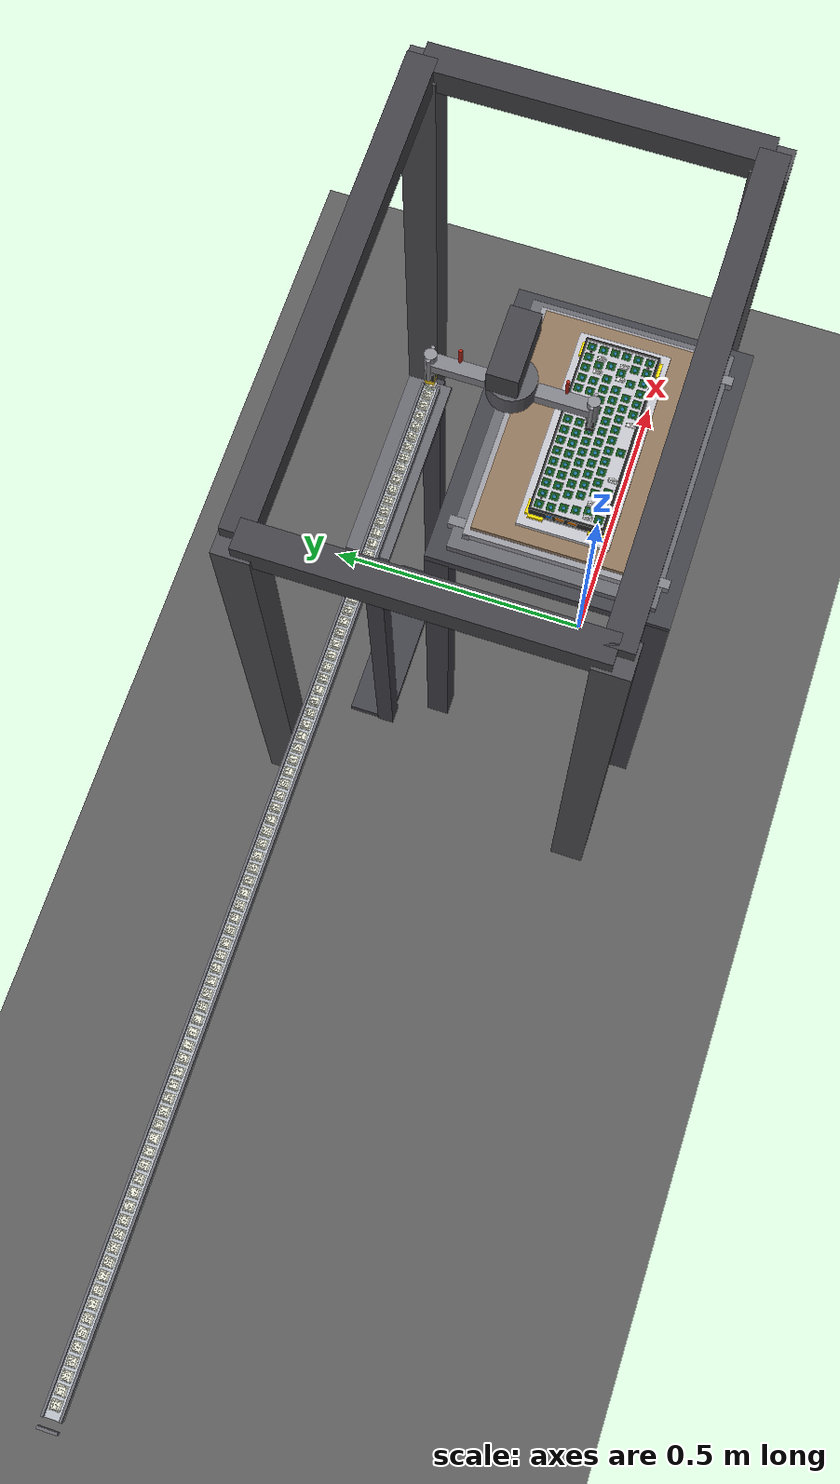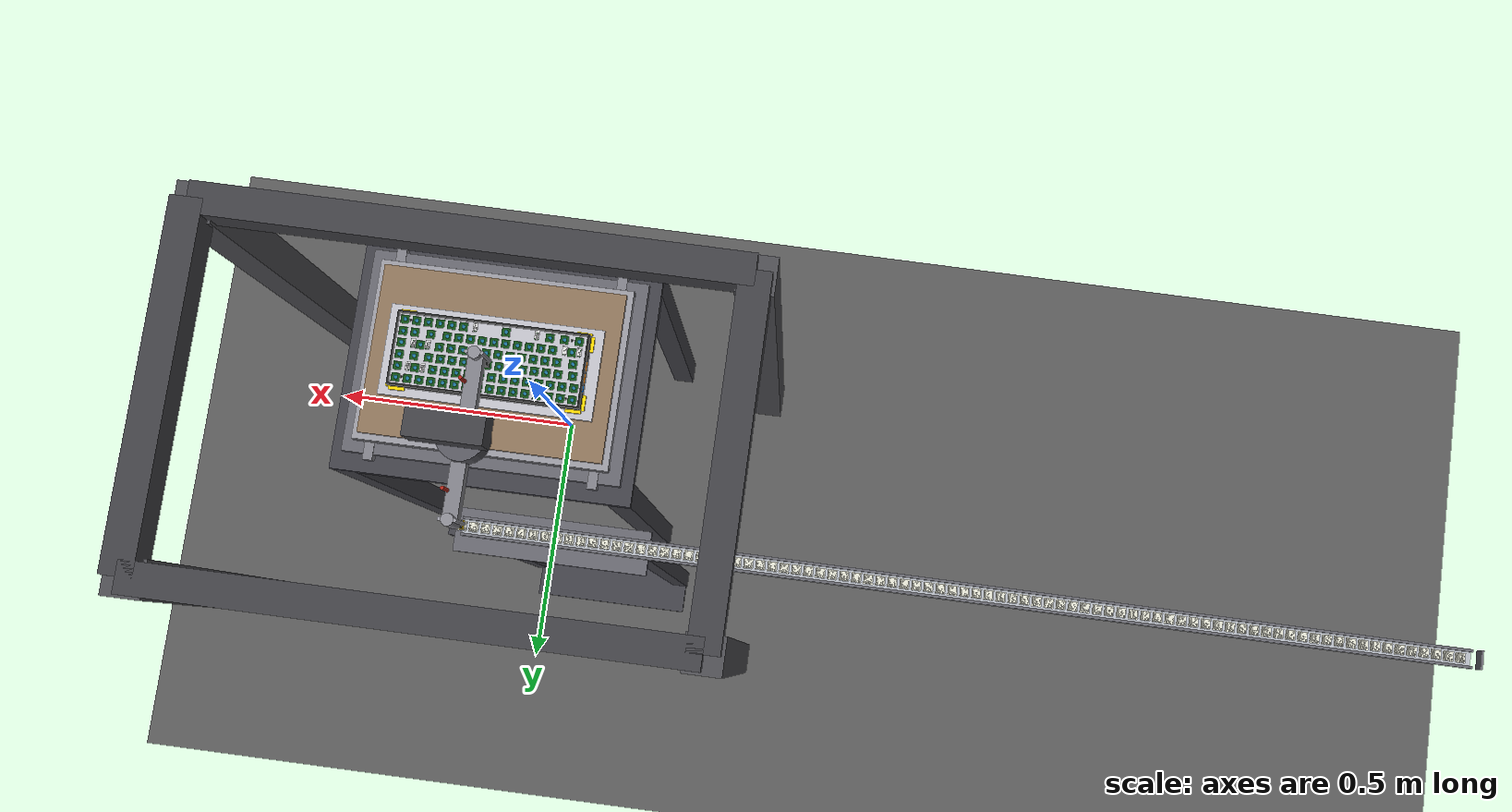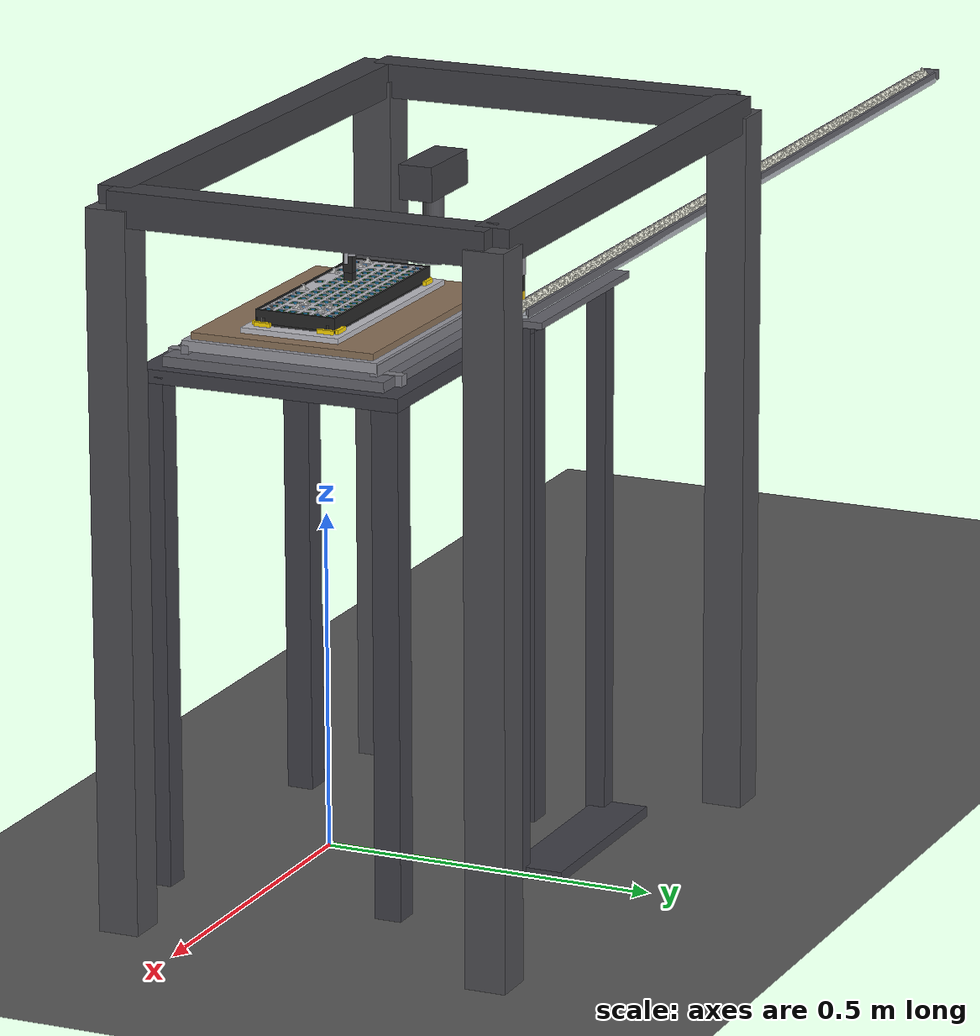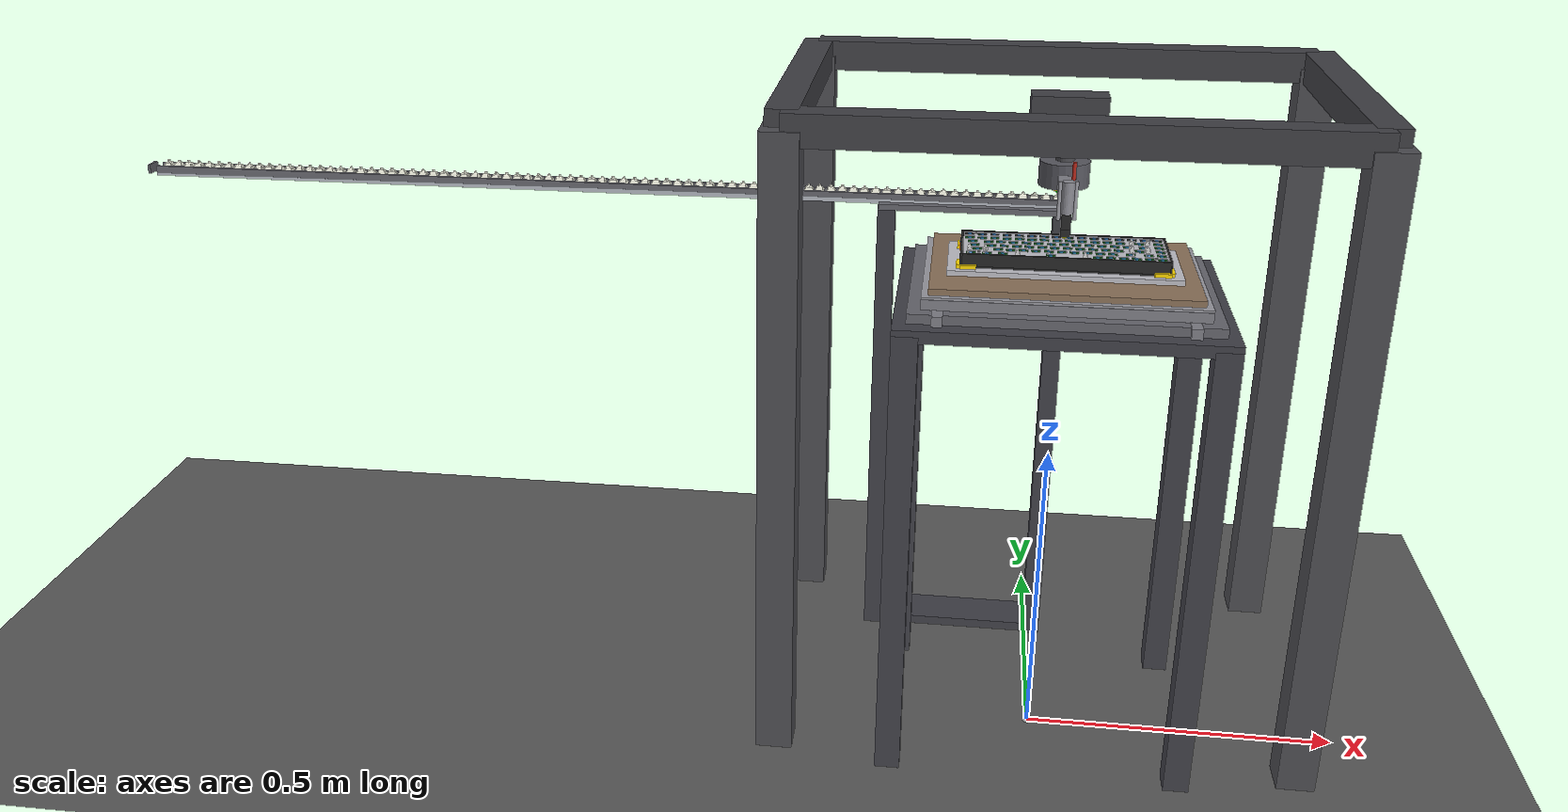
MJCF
<mujoco model="station3">

  <compiler angle="radian" autolimits="true"/>
  <option integrator="implicitfast"/>
<option integrator="implicitfast" solver="CG" iterations="20" ls_iterations="10"/>
  <visual>
    <headlight diffuse="0.6 0.6 0.6" ambient="0.3 0.3 0.3" specular="0 0 0"/>
    <rgba haze="0.15 0.25 0.35 1"/>
    <global azimuth="150" elevation="-25"/>
  </visual>

  <asset>
    <texture type="skybox" builtin="gradient" rgb1="0.3 0.5 0.7" rgb2="0 0 0"
             width="512" height="3072"/>
    <texture name="grid" type="2d" builtin="checker"
             rgb1="0.3 0.3 0.3" rgb2="0.4 0.4 0.4" width="512" height="512"/>
    <material name="floor_mat"      texture="grid" texrepeat="5 5" reflectance="0.2"/>
    <material name="aluminum_plate" rgba="0.75 0.75 0.78 1"
          specular="0.7" shininess="0.6" reflectance="0.20"/>
    <material name="fixture_stop"   rgba="1.0 0.85 0.0 1"/>
    <material name="mat_fr4"        rgba="0.06 0.30 0.08 1" specular="0.15" shininess="0.25"/>
    <material name="mat_epdm"       rgba="0.35 0.35 0.35 1" specular="0.02" shininess="0.02"/>
    <material name="mat_screw"      rgba="0.005 0.005 0.006 1" specular="0.35" shininess="0.35"/>
    <material name="stab_white"     rgba="0.86 0.86 0.86 1" specular="0.25" shininess="0.20"/>
    <material name="stab_wire"      rgba="0.70 0.70 0.72 1" specular="0.7" shininess="0.7"/>
    <material name="abs_plastic"    rgba="0.15 0.15 0.15 1"/>
    <material name="table_surface"  rgba="0.55 0.45 0.35 1"/>
    <material name="steel_dark"     rgba="0.25 0.25 0.28 1"/>
    <material name="steel_mid"      rgba="0.40 0.40 0.43 1"/>
    <material name="steel_light"    rgba="0.60 0.60 0.63 1"/>
    <material name="gantry_mat"     rgba="0.30 0.30 0.32 1"/>
    <material name="gantry_beam"    rgba="0.25 0.25 0.27 1"/>
    <material name="column_mat"     rgba="0.35 0.35 0.38 1"/>
    <material name="arm_mat"        rgba="0.50 0.50 0.53 1"/>
    <material name="head_body"      rgba="0.55 0.55 0.58 1"/>
    <material name="head_tip"       rgba="0.15 0.15 0.15 1"/>
    <material name="tray_mat"       rgba="0.70 0.72 0.75 1"/>
    <material name="slide_rail"     rgba="0.50 0.50 0.53 1"/>
    <!-- Switch mesh and materials (from switch_1u.xml) -->
    <material name="abs_dark"
          rgba="0.88 0.88 0.82 1"
          specular="0.15" shininess="0.25" reflectance="0.03"/>
    <material name="abs_dark_collision"
              rgba="0.12 0.12 0.12 0.0"/>
    <mesh name="switch_mesh"
          file="../meshes/Switch_Decimated.stl"
          scale="0.001 0.001 0.001"
          refpos="-7.350 0.053 -7.350"
          refquat="0.7071 -0.7071 0 0"/>
    <mesh name="aluminum_plate_mesh"
          file="../meshes/aluminum_plate.stl"
          scale="0.001 0.001 0.001"/>
    <mesh name="stabilizer_mesh"
          file="../meshes/Stabilizer_Decimated.stl"
          scale="0.001 0.001 0.001"
          refpos="-23.958 0.000 -1.712"
          refquat="0.7071 -0.7071 0 0"/>
  </asset>

  <worldbody>
    <light name="main_light" pos="0 0 3"     dir="0 0 -1"      directional="true"/>
    <light name="fill_light" pos="1 -1 2"    dir="-0.5 0.5 -1" directional="true"
           diffuse="0.3 0.3 0.3"/>
    <light name="work_light" pos="0 0.030 1.4" dir="0 0 -1"
           directional="false" diffuse="0.5 0.5 0.5"/>

    <geom name="floor" type="plane" size="3 3 0.05" material="floor_mat"/>

    <!-- World frame axis indicator -->
    <body name="axis_indicator" pos="0 0 0">
      <geom name="axis_x" type="cylinder" size="0.0025 0.100"
            pos="0.100 0 0.0025" euler="0 1.5708 0"
            rgba="1 0 0 1" contype="0" conaffinity="0"/>
      <geom name="axis_y" type="cylinder" size="0.0025 0.100"
            pos="0 0.100 0.0025" euler="1.5708 0 0"
            rgba="0 0.8 0 1" contype="0" conaffinity="0"/>
      <geom name="axis_z" type="cylinder" size="0.0025 0.100"
            pos="0 0 0.100"
            rgba="0 0 1 1" contype="0" conaffinity="0"/>
      <geom name="axis_origin" type="sphere" size="0.008"
            pos="0 0 0" rgba="1 1 1 1" contype="0" conaffinity="0"/>
    </body>

    <!--
      XY SLIDING TABLE
      Stack: table_base → y_slide → x_slide → table_top → pallet → case
    -->
    <body name="table_base" pos="0 0.030 0">
      <!-- 4 legs 750mm tall -->
      <geom name="leg_fl" type="box" size="0.020 0.020 0.375"
            pos="-0.230 -0.180 0.375" material="steel_dark" mass="5.0"/>
      <geom name="leg_fr" type="box" size="0.020 0.020 0.375"
            pos="0.230 -0.180 0.375"  material="steel_dark" mass="5.0"/>
      <geom name="leg_rl" type="box" size="0.020 0.020 0.375"
            pos="-0.230 0.180 0.375"  material="steel_dark" mass="5.0"/>
      <geom name="leg_rr" type="box" size="0.020 0.020 0.375"
            pos="0.230 0.180 0.375"   material="steel_dark" mass="5.0"/>
      <!-- Base plate top at z=0.760 -->
      <geom name="base_plate_xy" type="box" size="0.250 0.200 0.010"
            pos="0 0 0.750" material="steel_dark" mass="8.0"
            contype="1" conaffinity="1"/>
      <!-- Y-axis rails -->
      <geom name="rail_y_left"  type="box" size="0.008 0.180 0.008"
            pos="-0.185 0 0.768" material="slide_rail" mass="0.8"/>
      <geom name="rail_y_right" type="box" size="0.008 0.180 0.008"
            pos="0.185 0 0.768"  material="slide_rail" mass="0.8"/>

      <!-- Y SLIDE: 15mm thick, top at z=0.775 -->
      <body name="y_slide" pos="0 0 0.7675">
        <joint name="y_joint" type="slide" axis="0 1 0"
               range="-0.115 0.115" damping="10" stiffness="0"/>
        <geom name="y_slide_plate" type="box" size="0.230 0.170 0.0075"
              pos="0 0 0" material="steel_mid" mass="4.0"/>
        <!-- X-axis rails -->
        <geom name="rail_x_front" type="box" size="0.210 0.006 0.008"
              pos="0 -0.145 0.016" material="slide_rail" mass="0.4"/>
        <geom name="rail_x_rear"  type="box" size="0.210 0.006 0.008"
              pos="0 0.145 0.016"  material="slide_rail" mass="0.4"/>

        <!-- X SLIDE: 15mm thick, top at z=0.790 -->
        <body name="x_slide" pos="0 0 0.020">
          <joint name="x_joint" type="slide" axis="1 0 0"
                 range="-0.160 0.160" damping="10" stiffness="0"/>
          <geom name="x_slide_plate" type="box" size="0.210 0.150 0.0075"
                pos="0 0 0" material="steel_light" mass="3.0"/>

          <!-- TABLE TOP: surface at z=0.800 -->
          <body name="table_top_body" pos="0 0 0.0075">
            <geom name="table_top_surf" type="box" size="0.200 0.140 0.005"
                  pos="0 0 0.005" material="table_surface" mass="2.0"
                  contype="1" conaffinity="1"/>

            <!-- PALLET: top surface at z=0.810 -->
            <body name="pallet_base" pos="0 0 0.010">
              <!-- New 350mm x 150mm x 8mm pallet base.
                   S3 keeps body origin at pallet bottom face; top is z=+0.008. -->
              <geom name="base_plate" type="box" size="0.175 0.075 0.004"
                    pos="0 0 0.004" material="aluminum_plate" mass="1.5"
                    friction="0.8 0.005 0.0001" condim="4" priority="1"/>

              <!-- Updated corner fixture stops for 312.8mm x 122.3mm bottom case. -->
              <geom name="stop_FL_x" type="box" size="0.0125 0.0025 0.003" pos="-0.1439 -0.0637 0.011" material="fixture_stop" mass="0.02"/>
              <geom name="stop_FL_y" type="box" size="0.0025 0.0125 0.003" pos="-0.1589 -0.04865 0.011" material="fixture_stop" mass="0.02"/>
              <geom name="stop_FR_x" type="box" size="0.0125 0.0025 0.003" pos="0.1439 -0.0637 0.011" material="fixture_stop" mass="0.02"/>
              <geom name="stop_FR_y" type="box" size="0.0025 0.0125 0.003" pos="0.1589 -0.04865 0.011" material="fixture_stop" mass="0.02"/>
              <geom name="stop_RL_x" type="box" size="0.0125 0.0025 0.003" pos="-0.1439 0.0637 0.011" material="fixture_stop" mass="0.02"/>
              <geom name="stop_RL_y" type="box" size="0.0025 0.0125 0.003" pos="-0.1589 0.04865 0.011" material="fixture_stop" mass="0.02"/>
              <geom name="stop_RR_x" type="box" size="0.0125 0.0025 0.003" pos="0.1439 0.0637 0.011" material="fixture_stop" mass="0.02"/>
              <geom name="stop_RR_y" type="box" size="0.0025 0.0125 0.003" pos="0.1589 0.04865 0.011" material="fixture_stop" mass="0.02"/>

              <!-- BOTTOM CASE + S1 OUTPUT STACK. Body name and pos preserved. -->
              <body name="bottom_case" pos="0 0 0.020">
                <inertial pos="0 0 0" mass="0.085" diaginertia="3.2e-5 2.4e-4 2.5e-4"/>

                <!-- New bottom case visual: 312.8mm x 122.3mm x 22mm shell. -->
                <geom name="case_floor" type="box" size="0.1564 0.06115 0.0015" pos="0 0 -0.0095" material="abs_plastic" density="1050" friction="1.0 0.005 0.0001" condim="4" priority="1"/>
                <geom name="case_wall_left_A" type="box" size="0.0015 0.01433 0.0095" pos="-0.1549 0.04682 0.0015" material="abs_plastic" density="1050" friction="1.0 0.005 0.0001" condim="4" priority="1"/>
                <geom name="case_wall_left_usbc_below" type="box" size="0.0015 0.0045 0.0045" pos="-0.1549 0.028 -0.0035" material="abs_plastic" density="1050" friction="1.0 0.005 0.0001" condim="4" priority="1"/>
                <geom name="case_wall_left_usbc_above" type="box" size="0.0015 0.0045 0.003" pos="-0.1549 0.028 0.008" material="abs_plastic" density="1050" friction="1.0 0.005 0.0001" condim="4" priority="1"/>
                <geom name="case_wall_left_B" type="box" size="0.0015 0.003 0.0095" pos="-0.1549 0.0205 0.0015" material="abs_plastic" density="1050" friction="1.0 0.005 0.0001" condim="4" priority="1"/>
                <geom name="case_wall_left_pwr_below" type="box" size="0.0015 0.007 0.004" pos="-0.1549 0.0105 -0.004" material="abs_plastic" density="1050" friction="1.0 0.005 0.0001" condim="4" priority="1"/>
                <geom name="case_wall_left_pwr_above" type="box" size="0.0015 0.007 0.0025" pos="-0.1549 0.0105 0.0085" material="abs_plastic" density="1050" friction="1.0 0.005 0.0001" condim="4" priority="1"/>
                <geom name="case_wall_left_C" type="box" size="0.0015 0.005 0.0095" pos="-0.1549 -0.0005 0.0015" material="abs_plastic" density="1050" friction="1.0 0.005 0.0001" condim="4" priority="1"/>
                <geom name="case_wall_left_os_below" type="box" size="0.0015 0.007 0.004" pos="-0.1549 -0.0095 -0.004" material="abs_plastic" density="1050" friction="1.0 0.005 0.0001" condim="4" priority="1"/>
                <geom name="case_wall_left_os_above" type="box" size="0.0015 0.007 0.0025" pos="-0.1549 -0.0095 0.0085" material="abs_plastic" density="1050" friction="1.0 0.005 0.0001" condim="4" priority="1"/>
                <geom name="case_wall_left_D" type="box" size="0.0015 0.02233 0.0095" pos="-0.1549 -0.03883 0.0015" material="abs_plastic" density="1050" friction="1.0 0.005 0.0001" condim="4" priority="1"/>
                <site name="case_usbc_cutout" type="box" size="0.001 0.0045 0.002" pos="-0.1565 0.028 0.003" rgba="0 0.5 1 0.9"/>
                <site name="case_power_switch" type="box" size="0.001 0.007 0.002" pos="-0.1565 0.0105 0.003" rgba="1 0.5 0 0.9"/>
                <site name="case_os_switch" type="box" size="0.001 0.007 0.002" pos="-0.1565 -0.0095 0.003" rgba="1 0.5 0 0.9"/>
                <geom name="case_wall_right" type="box" size="0.0015 0.06115 0.0095" pos="0.1549 0 0.0015" material="abs_plastic" density="1050" friction="1.0 0.005 0.0001" condim="4" priority="1"/>
                <geom name="case_wall_rear" type="box" size="0.1564 0.0015 0.0095" pos="0 0.05965 0.0015" material="abs_plastic" density="1050" friction="1.0 0.005 0.0001" condim="4" priority="1"/>
                <geom name="case_wall_front" type="box" size="0.1564 0.0015 0.0095" pos="0 -0.05965 0.0015" material="abs_plastic" density="1050" friction="1.0 0.005 0.0001" condim="4" priority="1"/>
                <geom name="case_battery_rib_left" type="box" size="0.045 0.00075 0.002" pos="0.025 -0.03075 -0.006" material="abs_plastic" density="1050" friction="1.0 0.005 0.0001" condim="4" priority="1"/>
                <geom name="case_battery_rib_right" type="box" size="0.045 0.00075 0.002" pos="0.025 0.03075 -0.006" material="abs_plastic" density="1050" friction="1.0 0.005 0.0001" condim="4" priority="1"/>
                <geom name="case_battery_rib_front_left" type="box" size="0.00075 0.0125 0.002" pos="-0.02025 -0.0175 -0.006" material="abs_plastic" density="1050" friction="1.0 0.005 0.0001" condim="4" priority="1"/>
                <geom name="case_battery_rib_front_right" type="box" size="0.00075 0.0125 0.002" pos="-0.02025 0.0175 -0.006" material="abs_plastic" density="1050" friction="1.0 0.005 0.0001" condim="4" priority="1"/>
                <geom name="case_battery_rib_rear" type="box" size="0.00075 0.030 0.002" pos="0.07025 0 -0.006" material="abs_plastic" density="1050" friction="1.0 0.005 0.0001" condim="4" priority="1"/>
                <!-- Screw bosses copied from Station 1 final bottom case; visual-only for S3. -->
                <geom name="case_boss_FL" type="cylinder" size="0.003 0.004" pos="-0.1515 -0.0495 -0.004" material="abs_plastic" mass="0" contype="0" conaffinity="0"/>
                <geom name="case_boss_FR" type="cylinder" size="0.003 0.004" pos=" 0.1545 -0.0495 -0.004" material="abs_plastic" mass="0" contype="0" conaffinity="0"/>
                <geom name="case_boss_RL" type="cylinder" size="0.003 0.004" pos="-0.1515  0.0495 -0.004" material="abs_plastic" mass="0" contype="0" conaffinity="0"/>
                <geom name="case_boss_RR" type="cylinder" size="0.003 0.004" pos=" 0.1545  0.0495 -0.004" material="abs_plastic" mass="0" contype="0" conaffinity="0"/>

                <geom name="s3_screw_FL_shaft" type="cylinder" size="0.0014 0.005" pos=" 0.133561  0.047060 0.005" material="mat_screw" mass="0" contype="0" conaffinity="0"/>
                <geom name="s3_screw_FL_head"  type="cylinder" size="0.0020 0.001" pos=" 0.133561  0.047060 0.011" material="mat_screw" mass="0" contype="0" conaffinity="0"/>
                <geom name="s3_screw_FR_shaft" type="cylinder" size="0.0014 0.005" pos="-0.1329  0.0476 0.005" material="mat_screw" mass="0" contype="0" conaffinity="0"/>
                <geom name="s3_screw_FR_head"  type="cylinder" size="0.0020 0.001" pos="-0.1329  0.0476 0.011" material="mat_screw" mass="0" contype="0" conaffinity="0"/>
                <geom name="s3_screw_RL_shaft" type="cylinder" size="0.0014 0.005" pos=" 0.1334 -0.0468 0.005" material="mat_screw" mass="0" contype="0" conaffinity="0"/>
                <geom name="s3_screw_RL_head"  type="cylinder" size="0.0020 0.001" pos=" 0.1334 -0.0468 0.011" material="mat_screw" mass="0" contype="0" conaffinity="0"/>
                <geom name="s3_screw_RR_shaft" type="cylinder" size="0.0014 0.005" pos="-0.1288 -0.0472 0.005" material="mat_screw" mass="0" contype="0" conaffinity="0"/>
                <geom name="s3_screw_RR_head"  type="cylinder" size="0.0020 0.001" pos="-0.1288 -0.0472 0.011" material="mat_screw" mass="0" contype="0" conaffinity="0"/>
                <geom name="s3_epdm_front" type="box" size="0.1454 0.01408 0.00075" pos="0 -0.04408 -0.00625" material="mat_epdm" mass="0" contype="0" conaffinity="0"/>
                <geom name="s3_epdm_rear"  type="box" size="0.1454 0.01408 0.00075" pos="0  0.04408 -0.00625" material="mat_epdm" mass="0" contype="0" conaffinity="0"/>
                <geom name="s3_epdm_left"  type="box" size="0.06670 0.03000 0.00075" pos="-0.08670 0 -0.00625" material="mat_epdm" mass="0" contype="0" conaffinity="0"/>
                <geom name="s3_epdm_right" type="box" size="0.04170 0.03000 0.00075" pos=" 0.11170 0 -0.00625" material="mat_epdm" mass="0" contype="0" conaffinity="0"/>
                <geom name="s3_battery" type="box" size="0.043 0.028 0.003" pos="-0.060 0 -0.00250" mass="0" rgba="0.15 0.25 0.15 1" contype="0" conaffinity="0"/>
                <geom name="s3_pcb" type="box" size="0.1510 0.0560 0.0020" pos="0 0 0.00350" mass="0" material="mat_fr4" contype="0" conaffinity="0"/>
                <geom name="s3_pcb_usbc" type="box" size="0.0015 0.0045 0.0020" pos="-0.1525 0.0280 0.00450" mass="0" rgba="0.025 0.025 0.025 1" contype="0" conaffinity="0"/>
                <geom name="s3_pcb_pwr"  type="box" size="0.0015 0.0070 0.0030" pos="-0.1525 0.0105 0.00500" mass="0" rgba="0.025 0.025 0.025 1" contype="0" conaffinity="0"/>
                <geom name="s3_pcb_os"   type="box" size="0.0015 0.0070 0.0030" pos="-0.1525 -0.0095 0.00500" mass="0" rgba="0.025 0.025 0.025 1" contype="0" conaffinity="0"/>

                <!-- ALUMINUM PLATE BODY — name, position, and sw_* sites preserved. -->
                <body name="alu_plate" pos="0 0 0.00750">
                  <geom name="s3_alu_plate" type="mesh" mesh="aluminum_plate_mesh" pos="0.003361 0.00256 0.000747" mass="0" material="aluminum_plate" contype="0" conaffinity="0"/>
                  <!-- Stabilizers: visual-only, aligned to the shifted aluminum plate mesh. -->
                  <body name="s3_stab_space_L" pos="-0.071208 -0.048626 -0.00550"><geom name="s3_stab_space_L_mesh" type="mesh" mesh="stabilizer_mesh" pos="-0.047852 0.0017 0.00650" material="stab_white" contype="0" conaffinity="0"/></body>
                  <body name="s3_stab_space_R" pos="0.028792 -0.048626 -0.00550"><geom name="s3_stab_space_R_mesh" type="mesh" mesh="stabilizer_mesh" pos="-0.047852 0.0017 0.00650" material="stab_white" contype="0" conaffinity="0"/></body>
                  <body name="s3_stab_lshift_L" pos="-0.142688 -0.029576 -0.00550"><geom name="s3_stab_lshift_L_mesh" type="mesh" mesh="stabilizer_mesh" pos="-0.047852 0.0017 0.00650" material="stab_white" contype="0" conaffinity="0"/></body>
                  <body name="s3_stab_lshift_R" pos="-0.118808 -0.029576 -0.00550"><geom name="s3_stab_lshift_R_mesh" type="mesh" mesh="stabilizer_mesh" pos="-0.047852 0.0017 0.00650" material="stab_white" contype="0" conaffinity="0"/></body>
                  <body name="s3_stab_enter_L" pos="0.100202 -0.010516 -0.00550"><geom name="s3_stab_enter_L_mesh" type="mesh" mesh="stabilizer_mesh" pos="-0.047852 0.0017 0.00650" material="stab_white" contype="0" conaffinity="0"/></body>
                  <body name="s3_stab_enter_R" pos="0.124082 -0.010516 -0.00550"><geom name="s3_stab_enter_R_mesh" type="mesh" mesh="stabilizer_mesh" pos="-0.047852 0.0017 0.00650" material="stab_white" contype="0" conaffinity="0"/></body>
                  <body name="s3_stab_bksp_L" pos="0.102582 0.027584 -0.00550"><geom name="s3_stab_bksp_L_mesh" type="mesh" mesh="stabilizer_mesh" pos="-0.047852 0.0017 0.00650" material="stab_white" contype="0" conaffinity="0"/></body>
                  <body name="s3_stab_bksp_R" pos="0.126462 0.027584 -0.00550"><geom name="s3_stab_bksp_R_mesh" type="mesh" mesh="stabilizer_mesh" pos="-0.047852 0.0017 0.00650" material="stab_white" contype="0" conaffinity="0"/></body>
                  <!-- ROW 0 — Function row -->
                  <site name="sw_Esc"     type="cylinder" size="0.003 0.001" pos="-0.1429  0.0480 0.0015" rgba="0.2 0.6 1 0.6"/>
                  <site name="sw_F1"      type="cylinder" size="0.003 0.001" pos="-0.1238  0.0480 0.0015" rgba="0.2 0.6 1 0.6"/>
                  <site name="sw_F2"      type="cylinder" size="0.003 0.001" pos="-0.1048  0.0480 0.0015" rgba="0.2 0.6 1 0.6"/>
                  <site name="sw_F3"      type="cylinder" size="0.003 0.001" pos="-0.0857  0.0480 0.0015" rgba="0.2 0.6 1 0.6"/>
                  <site name="sw_F4"      type="cylinder" size="0.003 0.001" pos="-0.0667  0.0480 0.0015" rgba="0.2 0.6 1 0.6"/>
                  <site name="sw_F5"      type="cylinder" size="0.003 0.001" pos="-0.0476  0.0480 0.0015" rgba="0.2 0.6 1 0.6"/>
                  <site name="sw_F6"      type="cylinder" size="0.003 0.001" pos="-0.0286  0.0480 0.0015" rgba="0.2 0.6 1 0.6"/>
                  <site name="sw_F7"      type="cylinder" size="0.003 0.001" pos="-0.0095  0.0480 0.0015" rgba="0.2 0.6 1 0.6"/>
                  <site name="sw_F8"      type="cylinder" size="0.003 0.001" pos=" 0.0095  0.0480 0.0015" rgba="0.2 0.6 1 0.6"/>
                  <site name="sw_F9"      type="cylinder" size="0.003 0.001" pos=" 0.0286  0.0480 0.0015" rgba="0.2 0.6 1 0.6"/>
                  <site name="sw_F10"     type="cylinder" size="0.003 0.001" pos=" 0.0476  0.0480 0.0015" rgba="0.2 0.6 1 0.6"/>
                  <site name="sw_F11"     type="cylinder" size="0.003 0.001" pos=" 0.0667  0.0480 0.0015" rgba="0.2 0.6 1 0.6"/>
                  <site name="sw_F12"     type="cylinder" size="0.003 0.001" pos=" 0.0857  0.0480 0.0015" rgba="0.2 0.6 1 0.6"/>
                  <site name="sw_PrtSc"   type="cylinder" size="0.003 0.001" pos=" 0.1048  0.0480 0.0015" rgba="0.2 0.6 1 0.6"/>
                  <site name="sw_Pause"   type="cylinder" size="0.003 0.001" pos=" 0.1238  0.0480 0.0015" rgba="0.2 0.6 1 0.6"/>
                  <site name="sw_Del"     type="cylinder" size="0.003 0.001" pos=" 0.1429  0.0480 0.0015" rgba="0.2 0.6 1 0.6"/>
                  <!-- ROW 1 — Number row -->
                  <site name="sw_Grave"   type="cylinder" size="0.003 0.001" pos="-0.1429  0.0290 0.0015" rgba="0.2 0.6 1 0.6"/>
                  <site name="sw_1"       type="cylinder" size="0.003 0.001" pos="-0.1238  0.0290 0.0015" rgba="0.2 0.6 1 0.6"/>
                  <site name="sw_2"       type="cylinder" size="0.003 0.001" pos="-0.1048  0.0290 0.0015" rgba="0.2 0.6 1 0.6"/>
                  <site name="sw_3"       type="cylinder" size="0.003 0.001" pos="-0.0857  0.0290 0.0015" rgba="0.2 0.6 1 0.6"/>
                  <site name="sw_4"       type="cylinder" size="0.003 0.001" pos="-0.0667  0.0290 0.0015" rgba="0.2 0.6 1 0.6"/>
                  <site name="sw_5"       type="cylinder" size="0.003 0.001" pos="-0.0476  0.0290 0.0015" rgba="0.2 0.6 1 0.6"/>
                  <site name="sw_6"       type="cylinder" size="0.003 0.001" pos="-0.0286  0.0290 0.0015" rgba="0.2 0.6 1 0.6"/>
                  <site name="sw_7"       type="cylinder" size="0.003 0.001" pos="-0.0095  0.0290 0.0015" rgba="0.2 0.6 1 0.6"/>
                  <site name="sw_8"       type="cylinder" size="0.003 0.001" pos=" 0.0095  0.0290 0.0015" rgba="0.2 0.6 1 0.6"/>
                  <site name="sw_9"       type="cylinder" size="0.003 0.001" pos=" 0.0286  0.0290 0.0015" rgba="0.2 0.6 1 0.6"/>
                  <site name="sw_0"       type="cylinder" size="0.003 0.001" pos=" 0.0476  0.0290 0.0015" rgba="0.2 0.6 1 0.6"/>
                  <site name="sw_Minus"   type="cylinder" size="0.003 0.001" pos=" 0.0667  0.0290 0.0015" rgba="0.2 0.6 1 0.6"/>
                  <site name="sw_Equal"   type="cylinder" size="0.003 0.001" pos=" 0.0857  0.0290 0.0015" rgba="0.2 0.6 1 0.6"/>
                  <site name="sw_Bksp"    type="cylinder" size="0.003 0.001" pos=" 0.1143  0.0290 0.0015" rgba="0.2 0.6 1 0.6"/>
                  <site name="sw_PgUp"    type="cylinder" size="0.003 0.001" pos=" 0.1429  0.0290 0.0015" rgba="0.2 0.6 1 0.6"/>
                  <!-- ROW 2 — QWERTY row -->
                  <site name="sw_Tab"     type="cylinder" size="0.003 0.001" pos="-0.1381  0.0099 0.0015" rgba="0.2 0.6 1 0.6"/>
                  <site name="sw_Q"       type="cylinder" size="0.003 0.001" pos="-0.1143  0.0099 0.0015" rgba="0.2 0.6 1 0.6"/>
                  <site name="sw_W"       type="cylinder" size="0.003 0.001" pos="-0.0953  0.0099 0.0015" rgba="0.2 0.6 1 0.6"/>
                  <site name="sw_E"       type="cylinder" size="0.003 0.001" pos="-0.0762  0.0099 0.0015" rgba="0.2 0.6 1 0.6"/>
                  <site name="sw_R"       type="cylinder" size="0.003 0.001" pos="-0.0572  0.0099 0.0015" rgba="0.2 0.6 1 0.6"/>
                  <site name="sw_T"       type="cylinder" size="0.003 0.001" pos="-0.0381  0.0099 0.0015" rgba="0.2 0.6 1 0.6"/>
                  <site name="sw_Y"       type="cylinder" size="0.003 0.001" pos="-0.0191  0.0099 0.0015" rgba="0.2 0.6 1 0.6"/>
                  <site name="sw_U"       type="cylinder" size="0.003 0.001" pos=" 0.0000  0.0099 0.0015" rgba="0.2 0.6 1 0.6"/>
                  <site name="sw_I"       type="cylinder" size="0.003 0.001" pos=" 0.0191  0.0099 0.0015" rgba="0.2 0.6 1 0.6"/>
                  <site name="sw_O"       type="cylinder" size="0.003 0.001" pos=" 0.0381  0.0099 0.0015" rgba="0.2 0.6 1 0.6"/>
                  <site name="sw_P"       type="cylinder" size="0.003 0.001" pos=" 0.0572  0.0099 0.0015" rgba="0.2 0.6 1 0.6"/>
                  <site name="sw_LBrace"  type="cylinder" size="0.003 0.001" pos=" 0.0762  0.0099 0.0015" rgba="0.2 0.6 1 0.6"/>
                  <site name="sw_RBrace"  type="cylinder" size="0.003 0.001" pos=" 0.0953  0.0099 0.0015" rgba="0.2 0.6 1 0.6"/>
                  <site name="sw_Bkslash" type="cylinder" size="0.003 0.001" pos=" 0.1191  0.0099 0.0015" rgba="0.2 0.6 1 0.6"/>
                  <site name="sw_PgDn"    type="cylinder" size="0.003 0.001" pos=" 0.1429  0.0099 0.0015" rgba="0.2 0.6 1 0.6"/>
                  <!-- ROW 3 — Home row -->
                  <site name="sw_Caps"    type="cylinder" size="0.003 0.001" pos="-0.1357 -0.0092 0.0015" rgba="0.2 0.6 1 0.6"/>
                  <site name="sw_A"       type="cylinder" size="0.003 0.001" pos="-0.1095 -0.0092 0.0015" rgba="0.2 0.6 1 0.6"/>
                  <site name="sw_S"       type="cylinder" size="0.003 0.001" pos="-0.0905 -0.0092 0.0015" rgba="0.2 0.6 1 0.6"/>
                  <site name="sw_D"       type="cylinder" size="0.003 0.001" pos="-0.0714 -0.0092 0.0015" rgba="0.2 0.6 1 0.6"/>
                  <site name="sw_F"       type="cylinder" size="0.003 0.001" pos="-0.0524 -0.0092 0.0015" rgba="0.2 0.6 1 0.6"/>
                  <site name="sw_G"       type="cylinder" size="0.003 0.001" pos="-0.0333 -0.0092 0.0015" rgba="0.2 0.6 1 0.6"/>
                  <site name="sw_H"       type="cylinder" size="0.003 0.001" pos="-0.0143 -0.0092 0.0015" rgba="0.2 0.6 1 0.6"/>
                  <site name="sw_J"       type="cylinder" size="0.003 0.001" pos=" 0.0048 -0.0092 0.0015" rgba="0.2 0.6 1 0.6"/>
                  <site name="sw_K"       type="cylinder" size="0.003 0.001" pos=" 0.0238 -0.0092 0.0015" rgba="0.2 0.6 1 0.6"/>
                  <site name="sw_L"       type="cylinder" size="0.003 0.001" pos=" 0.0429 -0.0092 0.0015" rgba="0.2 0.6 1 0.6"/>
                  <site name="sw_Semicol" type="cylinder" size="0.003 0.001" pos=" 0.0619 -0.0092 0.0015" rgba="0.2 0.6 1 0.6"/>
                  <site name="sw_Quote"   type="cylinder" size="0.003 0.001" pos=" 0.0810 -0.0092 0.0015" rgba="0.2 0.6 1 0.6"/>
                  <site name="sw_Enter"   type="cylinder" size="0.003 0.001" pos=" 0.1119 -0.0092 0.0015" rgba="0.2 0.6 1 0.6"/>
                  <site name="sw_Home"    type="cylinder" size="0.003 0.001" pos=" 0.1429 -0.0092 0.0015" rgba="0.2 0.6 1 0.6"/>
                  <!-- ROW 4 — Shift row -->
                  <site name="sw_LShift"  type="cylinder" size="0.003 0.001" pos="-0.1310 -0.0282 0.0015" rgba="0.2 0.6 1 0.6"/>
                  <site name="sw_Z"       type="cylinder" size="0.003 0.001" pos="-0.1000 -0.0282 0.0015" rgba="0.2 0.6 1 0.6"/>
                  <site name="sw_X"       type="cylinder" size="0.003 0.001" pos="-0.0810 -0.0282 0.0015" rgba="0.2 0.6 1 0.6"/>
                  <site name="sw_C"       type="cylinder" size="0.003 0.001" pos="-0.0619 -0.0282 0.0015" rgba="0.2 0.6 1 0.6"/>
                  <site name="sw_V"       type="cylinder" size="0.003 0.001" pos="-0.0429 -0.0282 0.0015" rgba="0.2 0.6 1 0.6"/>
                  <site name="sw_B"       type="cylinder" size="0.003 0.001" pos="-0.0238 -0.0282 0.0015" rgba="0.2 0.6 1 0.6"/>
                  <site name="sw_N"       type="cylinder" size="0.003 0.001" pos="-0.0048 -0.0282 0.0015" rgba="0.2 0.6 1 0.6"/>
                  <site name="sw_M"       type="cylinder" size="0.003 0.001" pos=" 0.0143 -0.0282 0.0015" rgba="0.2 0.6 1 0.6"/>
                  <site name="sw_Comma"   type="cylinder" size="0.003 0.001" pos=" 0.0333 -0.0282 0.0015" rgba="0.2 0.6 1 0.6"/>
                  <site name="sw_Period"  type="cylinder" size="0.003 0.001" pos=" 0.0524 -0.0282 0.0015" rgba="0.2 0.6 1 0.6"/>
                  <site name="sw_Slash"   type="cylinder" size="0.003 0.001" pos=" 0.0714 -0.0282 0.0015" rgba="0.2 0.6 1 0.6"/>
                  <site name="sw_RShift"  type="cylinder" size="0.003 0.001" pos=" 0.0976 -0.0282 0.0015" rgba="0.2 0.6 1 0.6"/>
                  <site name="sw_Up"      type="cylinder" size="0.003 0.001" pos=" 0.1238 -0.0282 0.0015" rgba="0.2 0.6 1 0.6"/>
                  <site name="sw_End"     type="cylinder" size="0.003 0.001" pos=" 0.1429 -0.0282 0.0015" rgba="0.2 0.6 1 0.6"/>
                  <!-- ROW 5 — Bottom row -->
                  <site name="sw_LCtrl"  type="cylinder" size="0.003 0.001" pos="-0.1405 -0.0473 0.0015" rgba="0.2 0.6 1 0.6"/>
                  <site name="sw_LWin"   type="cylinder" size="0.003 0.001" pos="-0.1167 -0.0473 0.0015" rgba="0.2 0.6 1 0.6"/>
                  <site name="sw_LAlt"   type="cylinder" size="0.003 0.001" pos="-0.0929 -0.0473 0.0015" rgba="0.2 0.6 1 0.6"/>
                  <site name="sw_Space"  type="cylinder" size="0.003 0.001" pos="-0.0214 -0.0473 0.0015" rgba="0.2 0.6 1 0.6"/>
                  <site name="sw_RAlt"   type="cylinder" size="0.003 0.001" pos=" 0.0476 -0.0473 0.0015" rgba="0.2 0.6 1 0.6"/>
                  <site name="sw_Fn"     type="cylinder" size="0.003 0.001" pos=" 0.0667 -0.0473 0.0015" rgba="0.2 0.6 1 0.6"/>
                  <site name="sw_Left"   type="cylinder" size="0.003 0.001" pos=" 0.0857 -0.0473 0.0015" rgba="0.2 0.6 1 0.6"/>
                  <site name="sw_Down"   type="cylinder" size="0.003 0.001" pos=" 0.1048 -0.0473 0.0015" rgba="0.2 0.6 1 0.6"/>
                  <site name="sw_Right"  type="cylinder" size="0.003 0.001" pos=" 0.1238 -0.0473 0.0015" rgba="0.2 0.6 1 0.6"/>
                  <site name="sw_End2"   type="cylinder" size="0.003 0.001" pos=" 0.1429 -0.0473 0.0015" rgba="0.2 0.6 1 0.6"/>

                </body>
              </body>
            </body>
          </body>
        </body>
      </body>
    </body>

    <!--
      4-POST GANTRY FRAME (fixed)
      Straddles both table and feeder
      Posts at X=±0.420, front at Y=-0.250, rear at Y=+0.310
    -->
    <body name="gantry_frame" pos="0 0 0">
      <geom name="post_FL" type="box" size="0.030 0.030 0.519"
            pos="-0.420 -0.110 0.519" material="gantry_mat" mass="8.0"/>
      <geom name="post_FR" type="box" size="0.030 0.030 0.519"
            pos="0.420 -0.110 0.519"  material="gantry_mat" mass="8.0"/>
      <geom name="post_RL" type="box" size="0.030 0.030 0.519"
            pos="-0.420 0.450 0.519"  material="gantry_mat" mass="8.0"/>
      <geom name="post_RR" type="box" size="0.030 0.030 0.519"
            pos="0.420 0.450 0.519"   material="gantry_mat" mass="8.0"/>
      <!-- Top frame beams -->
      <geom name="beam_front" type="box" size="0.420 0.025 0.025"
            pos="0 -0.110 1.039" material="gantry_beam" mass="3.0"/>
      <geom name="beam_rear"  type="box" size="0.420 0.025 0.025"
            pos="0 0.450 1.039"  material="gantry_beam" mass="3.0"/>
      <geom name="beam_left"  type="box" size="0.025 0.280 0.025"
            pos="-0.420 0.170 1.039" material="gantry_beam" mass="2.0"/>
      <geom name="beam_right" type="box" size="0.025 0.280 0.025"
            pos="0.420 0.170 1.039"  material="gantry_beam" mass="2.0"/>
      <!-- Central support beam -->
      <geom name="beam_center" type="box" size="0.060 0.025 0.025"
            pos="0 0.170 1.014" material="gantry_beam" mass="1.5"/>
      <!-- Vertical drop shaft from center beam to rotating column -->
      <geom name="drop_shaft" type="cylinder" size="0.015 0.035"
            pos="0 0.170 0.964" material="gantry_mat" mass="0.5"
            contype="0" conaffinity="0"/>
    </body>

    <body name="rotating_column" pos="0 0.170 0.914">
      <joint name="column_rotation" type="hinge" axis="0 0 1"
             range="-3.1416 3.1416" damping="2" stiffness="0"/>

      <!-- Main column disc: 80mm dia, 40mm tall -->
      <geom name="column_disc" type="cylinder" size="0.040 0.020"
            pos="0 0 0" material="column_mat" mass="3.0"/>

      <!-- === ARM 1: extends in -Y direction toward keyboard === -->
      <geom name="arm_1" type="box" size="0.012 0.045 0.010"
            pos="0 -0.085 -0.005" material="arm_mat" mass="0.3"/>

      <!-- === ARM 2: extends in +Y direction toward feeder === -->
      <geom name="arm_2" type="box" size="0.012 0.045 0.010"
            pos="0 0.085 -0.005" material="arm_mat" mass="0.3"/>

      <!-- HEAD 1 SLIDE: Z motion toward keyboard (-Y arm) -->
      <body name="head_1_slide" pos="0 0 0">
        <inertial pos="0 0 0" mass="0.01" diaginertia="1e-6 1e-6 1e-6"/>
        <joint name="head_1_z" type="slide" axis="0 0 1"
               range="-0.150 0" damping="50" stiffness="0"/>
        <geom name="head_1_body" type="cylinder" size="0.010 0.025"
              pos="0 -0.130 -0.005" material="head_body" mass="0.5"/>
        <geom name="rod_1_L" type="cylinder" size="0.003 0.030"
              pos="-0.012 -0.130 -0.010" material="steel_light" mass="0.05"
              contype="0" conaffinity="0"/>
        <geom name="rod_1_R" type="cylinder" size="0.003 0.030"
              pos="0.012 -0.130 -0.010" material="steel_light" mass="0.05"
              contype="0" conaffinity="0"/>
        <geom name="head_1_tip" type="box" size="0.007 0.007 0.012"
              pos="0 -0.130 -0.042" material="head_tip" mass="0.1"/>
        <geom name="switch_1" type="box" size="0.007 0.007 0.006"
              pos="0 -0.130 -0.060" rgba="0.15 0.15 0.15 1"
              contype="0" conaffinity="0"/>
        <geom name="hose_1" type="cylinder" size="0.003 0.020"
              pos="0.010 -0.085 0.018"
              rgba="0.7 0.15 0.10 1" contype="0" conaffinity="0"/>
        <site name="head_1_tip_site" pos="0 -0.130 -0.066"
              size="0.004" rgba="1 1 0 0.9"/>
      </body>

      <!-- HEAD 2 SLIDE: Z motion toward feeder (+Y arm) -->
      <body name="head_2_slide" pos="0 0 0">
        <inertial pos="0 0 0" mass="0.01" diaginertia="1e-6 1e-6 1e-6"/>
        <joint name="head_2_z" type="slide" axis="0 0 1"
               range="-0.150 0" damping="50" stiffness="0"/>
        <geom name="head_2_body" type="cylinder" size="0.010 0.025"
              pos="0 0.130 -0.005" material="head_body" mass="0.5"/>
        <geom name="rod_2_L" type="cylinder" size="0.003 0.030"
              pos="-0.012 0.130 -0.010" material="steel_light" mass="0.05"
              contype="0" conaffinity="0"/>
        <geom name="rod_2_R" type="cylinder" size="0.003 0.030"
              pos="0.012 0.130 -0.010" material="steel_light" mass="0.05"
              contype="0" conaffinity="0"/>
        <geom name="head_2_tip" type="box" size="0.007 0.007 0.012"
              pos="0 0.130 -0.042" material="head_tip" mass="0.1"/>
        <geom name="switch_2" type="box" size="0.007 0.007 0.006"
              pos="0 0.130 -0.060" rgba="0.9 0.75 0.1 1"
              contype="0" conaffinity="0"/>
        <geom name="hose_2" type="cylinder" size="0.003 0.020"
              pos="0.010 0.085 0.018"
              rgba="0.7 0.15 0.10 1" contype="0" conaffinity="0"/>
        <site name="head_2_tip_site" pos="0 0.130 -0.066"
              size="0.004" rgba="0 1 0 0.9"/>
      </body>

    </body>

    <body name="tray_feeder" pos="0 0.330 0">

      <!-- Fixture stand: 2 legs supporting the tray at both X ends -->
      <geom name="feeder_leg_FL" type="box" size="0.015 0.015 0.4056"
            pos="-0.285 -0.030 0.4056" material="steel_dark" mass="2.0"
            contype="0" conaffinity="0"/>
      <geom name="feeder_leg_FR" type="box" size="0.015 0.015 0.4056"
            pos="0.010 -0.030 0.4056"  material="steel_dark" mass="2.0"
            contype="0" conaffinity="0"/>
      <!-- Base plate connecting legs -->
      <geom name="feeder_base" type="box" size="0.155 0.040 0.008"
            pos="-0.143 0 0.008" material="steel_dark" mass="2.0"
            contype="0" conaffinity="0"/>
      <!-- Tray support shelf -->
      <geom name="tray_shelf" type="box" size="0.155 0.035 0.005"
            pos="-0.143 -0.025 0.8161" material="steel_mid" mass="1.0"
            contype="0" conaffinity="0"/>

      <!-- Tray body: covers x=0 to x=-0.286, center at x=-0.143, half=0.155 -->
      <geom name="tray_body" type="box" size="0.800 0.015 0.004"
            pos="-0.800 -0.030 0.8221" material="tray_mat" mass="6.0"
            contype="0" conaffinity="0"/>
      <!-- Tray side rails (full length) -->
      <geom name="tray_rail_F" type="box" size="0.800 0.002 0.006"
            pos="-0.800 -0.043 0.8291" material="steel_mid" mass="0.8"
            contype="0" conaffinity="0"/>
      <geom name="tray_rail_R" type="box" size="0.800 0.002 0.006"
            pos="-0.800 -0.017 0.8291" material="steel_mid" mass="0.8"
            contype="0" conaffinity="0"/>
      <!-- Far end stop at x=-1.600 -->
      <geom name="tray_rail_back" type="box" size="0.002 0.015 0.008"
            pos="-1.614 -0.030 0.8281" material="steel_mid" mass="0.1"
            contype="0" conaffinity="0"/>

      <!-- Sensor detection site at pick position (x=0, y=0.310 world) -->
      <!-- Pick position site -->
      <site name="pick_position" pos="0 -0.030 0.8261"
            size="0.006" rgba="0 1 0 0.9"/>
    </body>

    <!-- Cameras -->
    <camera name="station3_overview"
            pos="0.8 -0.8 1.6"
            xyaxes="0.7 0.7 0 -0.35 0.35 0.87"/>
    <camera name="head_closeup"
            pos="0.3 -0.3 1.3"
            xyaxes="0.7 0.7 0 -0.4 0.4 0.82"/>
    <camera name="top_down"
            pos="0 0.030 2.0"
            xyaxes="1 0 0 0 1 0"/>
    <camera name="feeder_side"
            pos="0.6 0.4 1.2"
            xyaxes="-0.6 0.8 0 -0.4 -0.3 0.87"/>

    <body name="sw_Esc" pos="0.0000 0.3 0.82455">
      <freejoint name="swj_Esc"/>
      <geom name="swg_Esc"
            type="mesh" mesh="switch_mesh"
            pos="-0.01475 0 0.00945"
            material="abs_dark"
            contype="0" conaffinity="0"/>
    </body>

    <body name="sw_F1" pos="-0.0191 0.3 0.82455">
      <freejoint name="swj_F1"/>
      <geom name="swg_F1"
            type="mesh" mesh="switch_mesh"
            pos="-0.01475 0 0.00945"
            material="abs_dark"
            contype="0" conaffinity="0"/>
    </body>

    <body name="sw_F2" pos="-0.0381 0.3 0.82455">
      <freejoint name="swj_F2"/>
      <geom name="swg_F2"
            type="mesh" mesh="switch_mesh"
            pos="-0.01475 0 0.00945"
            material="abs_dark"
            contype="0" conaffinity="0"/>
    </body>

    <body name="sw_F3" pos="-0.0572 0.3 0.82455">
      <freejoint name="swj_F3"/>
      <geom name="swg_F3"
            type="mesh" mesh="switch_mesh"
            pos="-0.01475 0 0.00945"
            material="abs_dark"
            contype="0" conaffinity="0"/>
    </body>

    <body name="sw_F4" pos="-0.0762 0.3 0.82455">
      <freejoint name="swj_F4"/>
      <geom name="swg_F4"
            type="mesh" mesh="switch_mesh"
            pos="-0.01475 0 0.00945"
            material="abs_dark"
            contype="0" conaffinity="0"/>
    </body>

    <body name="sw_F5" pos="-0.0953 0.3 0.82455">
      <freejoint name="swj_F5"/>
      <geom name="swg_F5"
            type="mesh" mesh="switch_mesh"
            pos="-0.01475 0 0.00945"
            material="abs_dark"
            contype="0" conaffinity="0"/>
    </body>

    <body name="sw_F6" pos="-0.1143 0.3 0.82455">
      <freejoint name="swj_F6"/>
      <geom name="swg_F6"
            type="mesh" mesh="switch_mesh"
            pos="-0.01475 0 0.00945"
            material="abs_dark"
            contype="0" conaffinity="0"/>
    </body>

    <body name="sw_F7" pos="-0.1333 0.3 0.82455">
      <freejoint name="swj_F7"/>
      <geom name="swg_F7"
            type="mesh" mesh="switch_mesh"
            pos="-0.01475 0 0.00945"
            material="abs_dark"
            contype="0" conaffinity="0"/>
    </body>

    <body name="sw_F8" pos="-0.1524 0.3 0.82455">
      <freejoint name="swj_F8"/>
      <geom name="swg_F8"
            type="mesh" mesh="switch_mesh"
            pos="-0.01475 0 0.00945"
            material="abs_dark"
            contype="0" conaffinity="0"/>
    </body>

    <body name="sw_F9" pos="-0.1715 0.3 0.82455">
      <freejoint name="swj_F9"/>
      <geom name="swg_F9"
            type="mesh" mesh="switch_mesh"
            pos="-0.01475 0 0.00945"
            material="abs_dark"
            contype="0" conaffinity="0"/>
    </body>

    <body name="sw_F10" pos="-0.1905 0.3 0.82455">
      <freejoint name="swj_F10"/>
      <geom name="swg_F10"
            type="mesh" mesh="switch_mesh"
            pos="-0.01475 0 0.00945"
            material="abs_dark"
            contype="0" conaffinity="0"/>
    </body>

    <body name="sw_F11" pos="-0.2096 0.3 0.82455">
      <freejoint name="swj_F11"/>
      <geom name="swg_F11"
            type="mesh" mesh="switch_mesh"
            pos="-0.01475 0 0.00945"
            material="abs_dark"
            contype="0" conaffinity="0"/>
    </body>

    <body name="sw_F12" pos="-0.2286 0.3 0.82455">
      <freejoint name="swj_F12"/>
      <geom name="swg_F12"
            type="mesh" mesh="switch_mesh"
            pos="-0.01475 0 0.00945"
            material="abs_dark"
            contype="0" conaffinity="0"/>
    </body>

    <body name="sw_PrtSc" pos="-0.2477 0.3 0.82455">
      <freejoint name="swj_PrtSc"/>
      <geom name="swg_PrtSc"
            type="mesh" mesh="switch_mesh"
            pos="-0.01475 0 0.00945"
            material="abs_dark"
            contype="0" conaffinity="0"/>
    </body>

    <body name="sw_Pause" pos="-0.2667 0.3 0.82455">
      <freejoint name="swj_Pause"/>
      <geom name="swg_Pause"
            type="mesh" mesh="switch_mesh"
            pos="-0.01475 0 0.00945"
            material="abs_dark"
            contype="0" conaffinity="0"/>
    </body>

    <body name="sw_Del" pos="-0.2858 0.3 0.82455">
      <freejoint name="swj_Del"/>
      <geom name="swg_Del"
            type="mesh" mesh="switch_mesh"
            pos="-0.01475 0 0.00945"
            material="abs_dark"
            contype="0" conaffinity="0"/>
    </body>

    <body name="sw_Grave" pos="-0.3048 0.3 0.82455">
      <freejoint name="swj_Grave"/>
      <geom name="swg_Grave"
            type="mesh" mesh="switch_mesh"
            pos="-0.01475 0 0.00945"
            material="abs_dark"
            contype="0" conaffinity="0"/>
    </body>

    <body name="sw_1" pos="-0.3239 0.3 0.82455">
      <freejoint name="swj_1"/>
      <geom name="swg_1"
            type="mesh" mesh="switch_mesh"
            pos="-0.01475 0 0.00945"
            material="abs_dark"
            contype="0" conaffinity="0"/>
    </body>

    <body name="sw_2" pos="-0.3429 0.3 0.82455">
      <freejoint name="swj_2"/>
      <geom name="swg_2"
            type="mesh" mesh="switch_mesh"
            pos="-0.01475 0 0.00945"
            material="abs_dark"
            contype="0" conaffinity="0"/>
    </body>

    <body name="sw_3" pos="-0.3619 0.3 0.82455">
      <freejoint name="swj_3"/>
      <geom name="swg_3"
            type="mesh" mesh="switch_mesh"
            pos="-0.01475 0 0.00945"
            material="abs_dark"
            contype="0" conaffinity="0"/>
    </body>

    <body name="sw_4" pos="-0.3810 0.3 0.82455">
      <freejoint name="swj_4"/>
      <geom name="swg_4"
            type="mesh" mesh="switch_mesh"
            pos="-0.01475 0 0.00945"
            material="abs_dark"
            contype="0" conaffinity="0"/>
    </body>

    <body name="sw_5" pos="-0.4001 0.3 0.82455">
      <freejoint name="swj_5"/>
      <geom name="swg_5"
            type="mesh" mesh="switch_mesh"
            pos="-0.01475 0 0.00945"
            material="abs_dark"
            contype="0" conaffinity="0"/>
    </body>

    <body name="sw_6" pos="-0.4191 0.3 0.82455">
      <freejoint name="swj_6"/>
      <geom name="swg_6"
            type="mesh" mesh="switch_mesh"
            pos="-0.01475 0 0.00945"
            material="abs_dark"
            contype="0" conaffinity="0"/>
    </body>

    <body name="sw_7" pos="-0.4382 0.3 0.82455">
      <freejoint name="swj_7"/>
      <geom name="swg_7"
            type="mesh" mesh="switch_mesh"
            pos="-0.01475 0 0.00945"
            material="abs_dark"
            contype="0" conaffinity="0"/>
    </body>

    <body name="sw_8" pos="-0.4572 0.3 0.82455">
      <freejoint name="swj_8"/>
      <geom name="swg_8"
            type="mesh" mesh="switch_mesh"
            pos="-0.01475 0 0.00945"
            material="abs_dark"
            contype="0" conaffinity="0"/>
    </body>

    <body name="sw_9" pos="-0.4763 0.3 0.82455">
      <freejoint name="swj_9"/>
      <geom name="swg_9"
            type="mesh" mesh="switch_mesh"
            pos="-0.01475 0 0.00945"
            material="abs_dark"
            contype="0" conaffinity="0"/>
    </body>

    <body name="sw_0" pos="-0.4953 0.3 0.82455">
      <freejoint name="swj_0"/>
      <geom name="swg_0"
            type="mesh" mesh="switch_mesh"
            pos="-0.01475 0 0.00945"
            material="abs_dark"
            contype="0" conaffinity="0"/>
    </body>

    <body name="sw_Minus" pos="-0.5143 0.3 0.82455">
      <freejoint name="swj_Minus"/>
      <geom name="swg_Minus"
            type="mesh" mesh="switch_mesh"
            pos="-0.01475 0 0.00945"
            material="abs_dark"
            contype="0" conaffinity="0"/>
    </body>

    <body name="sw_Equal" pos="-0.5334 0.3 0.82455">
      <freejoint name="swj_Equal"/>
      <geom name="swg_Equal"
            type="mesh" mesh="switch_mesh"
            pos="-0.01475 0 0.00945"
            material="abs_dark"
            contype="0" conaffinity="0"/>
    </body>

    <body name="sw_Bksp" pos="-0.5524 0.3 0.82455">
      <freejoint name="swj_Bksp"/>
      <geom name="swg_Bksp"
            type="mesh" mesh="switch_mesh"
            pos="-0.01475 0 0.00945"
            material="abs_dark"
            contype="0" conaffinity="0"/>
    </body>

    <body name="sw_PgUp" pos="-0.5715 0.3 0.82455">
      <freejoint name="swj_PgUp"/>
      <geom name="swg_PgUp"
            type="mesh" mesh="switch_mesh"
            pos="-0.01475 0 0.00945"
            material="abs_dark"
            contype="0" conaffinity="0"/>
    </body>

    <body name="sw_Tab" pos="-0.5906 0.3 0.82455">
      <freejoint name="swj_Tab"/>
      <geom name="swg_Tab"
            type="mesh" mesh="switch_mesh"
            pos="-0.01475 0 0.00945"
            material="abs_dark"
            contype="0" conaffinity="0"/>
    </body>

    <body name="sw_Q" pos="-0.6096 0.3 0.82455">
      <freejoint name="swj_Q"/>
      <geom name="swg_Q"
            type="mesh" mesh="switch_mesh"
            pos="-0.01475 0 0.00945"
            material="abs_dark"
            contype="0" conaffinity="0"/>
    </body>

    <body name="sw_W" pos="-0.6287 0.3 0.82455">
      <freejoint name="swj_W"/>
      <geom name="swg_W"
            type="mesh" mesh="switch_mesh"
            pos="-0.01475 0 0.00945"
            material="abs_dark"
            contype="0" conaffinity="0"/>
    </body>

    <body name="sw_E" pos="-0.6477 0.3 0.82455">
      <freejoint name="swj_E"/>
      <geom name="swg_E"
            type="mesh" mesh="switch_mesh"
            pos="-0.01475 0 0.00945"
            material="abs_dark"
            contype="0" conaffinity="0"/>
    </body>

    <body name="sw_R" pos="-0.6668 0.3 0.82455">
      <freejoint name="swj_R"/>
      <geom name="swg_R"
            type="mesh" mesh="switch_mesh"
            pos="-0.01475 0 0.00945"
            material="abs_dark"
            contype="0" conaffinity="0"/>
    </body>

    <body name="sw_T" pos="-0.6858 0.3 0.82455">
      <freejoint name="swj_T"/>
      <geom name="swg_T"
            type="mesh" mesh="switch_mesh"
            pos="-0.01475 0 0.00945"
            material="abs_dark"
            contype="0" conaffinity="0"/>
    </body>

    <body name="sw_Y" pos="-0.7049 0.3 0.82455">
      <freejoint name="swj_Y"/>
      <geom name="swg_Y"
            type="mesh" mesh="switch_mesh"
            pos="-0.01475 0 0.00945"
            material="abs_dark"
            contype="0" conaffinity="0"/>
    </body>

    <body name="sw_U" pos="-0.7239 0.3 0.82455">
      <freejoint name="swj_U"/>
      <geom name="swg_U"
            type="mesh" mesh="switch_mesh"
            pos="-0.01475 0 0.00945"
            material="abs_dark"
            contype="0" conaffinity="0"/>
    </body>

    <body name="sw_I" pos="-0.7429 0.3 0.82455">
      <freejoint name="swj_I"/>
      <geom name="swg_I"
            type="mesh" mesh="switch_mesh"
            pos="-0.01475 0 0.00945"
            material="abs_dark"
            contype="0" conaffinity="0"/>
    </body>

    <body name="sw_O" pos="-0.7620 0.3 0.82455">
      <freejoint name="swj_O"/>
      <geom name="swg_O"
            type="mesh" mesh="switch_mesh"
            pos="-0.01475 0 0.00945"
            material="abs_dark"
            contype="0" conaffinity="0"/>
    </body>

    <body name="sw_P" pos="-0.7811 0.3 0.82455">
      <freejoint name="swj_P"/>
      <geom name="swg_P"
            type="mesh" mesh="switch_mesh"
            pos="-0.01475 0 0.00945"
            material="abs_dark"
            contype="0" conaffinity="0"/>
    </body>

    <body name="sw_LBrace" pos="-0.8001 0.3 0.82455">
      <freejoint name="swj_LBrace"/>
      <geom name="swg_LBrace"
            type="mesh" mesh="switch_mesh"
            pos="-0.01475 0 0.00945"
            material="abs_dark"
            contype="0" conaffinity="0"/>
    </body>

    <body name="sw_RBrace" pos="-0.8192 0.3 0.82455">
      <freejoint name="swj_RBrace"/>
      <geom name="swg_RBrace"
            type="mesh" mesh="switch_mesh"
            pos="-0.01475 0 0.00945"
            material="abs_dark"
            contype="0" conaffinity="0"/>
    </body>

    <body name="sw_Bkslash" pos="-0.8382 0.3 0.82455">
      <freejoint name="swj_Bkslash"/>
      <geom name="swg_Bkslash"
            type="mesh" mesh="switch_mesh"
            pos="-0.01475 0 0.00945"
            material="abs_dark"
            contype="0" conaffinity="0"/>
    </body>

    <body name="sw_PgDn" pos="-0.8573 0.3 0.82455">
      <freejoint name="swj_PgDn"/>
      <geom name="swg_PgDn"
            type="mesh" mesh="switch_mesh"
            pos="-0.01475 0 0.00945"
            material="abs_dark"
            contype="0" conaffinity="0"/>
    </body>

    <body name="sw_Caps" pos="-0.8763 0.3 0.82455">
      <freejoint name="swj_Caps"/>
      <geom name="swg_Caps"
            type="mesh" mesh="switch_mesh"
            pos="-0.01475 0 0.00945"
            material="abs_dark"
            contype="0" conaffinity="0"/>
    </body>

    <body name="sw_A" pos="-0.8954 0.3 0.82455">
      <freejoint name="swj_A"/>
      <geom name="swg_A"
            type="mesh" mesh="switch_mesh"
            pos="-0.01475 0 0.00945"
            material="abs_dark"
            contype="0" conaffinity="0"/>
    </body>

    <body name="sw_S" pos="-0.9144 0.3 0.82455">
      <freejoint name="swj_S"/>
      <geom name="swg_S"
            type="mesh" mesh="switch_mesh"
            pos="-0.01475 0 0.00945"
            material="abs_dark"
            contype="0" conaffinity="0"/>
    </body>

    <body name="sw_D" pos="-0.9335 0.3 0.82455">
      <freejoint name="swj_D"/>
      <geom name="swg_D"
            type="mesh" mesh="switch_mesh"
            pos="-0.01475 0 0.00945"
            material="abs_dark"
            contype="0" conaffinity="0"/>
    </body>

    <body name="sw_F" pos="-0.9525 0.3 0.82455">
      <freejoint name="swj_F"/>
      <geom name="swg_F"
            type="mesh" mesh="switch_mesh"
            pos="-0.01475 0 0.00945"
            material="abs_dark"
            contype="0" conaffinity="0"/>
    </body>

    <body name="sw_G" pos="-0.9716 0.3 0.82455">
      <freejoint name="swj_G"/>
      <geom name="swg_G"
            type="mesh" mesh="switch_mesh"
            pos="-0.01475 0 0.00945"
            material="abs_dark"
            contype="0" conaffinity="0"/>
    </body>

    <body name="sw_H" pos="-0.9906 0.3 0.82455">
      <freejoint name="swj_H"/>
      <geom name="swg_H"
            type="mesh" mesh="switch_mesh"
            pos="-0.01475 0 0.00945"
            material="abs_dark"
            contype="0" conaffinity="0"/>
    </body>

    <body name="sw_J" pos="-1.0097 0.3 0.82455">
      <freejoint name="swj_J"/>
      <geom name="swg_J"
            type="mesh" mesh="switch_mesh"
            pos="-0.01475 0 0.00945"
            material="abs_dark"
            contype="0" conaffinity="0"/>
    </body>

    <body name="sw_K" pos="-1.0287 0.3 0.82455">
      <freejoint name="swj_K"/>
      <geom name="swg_K"
            type="mesh" mesh="switch_mesh"
            pos="-0.01475 0 0.00945"
            material="abs_dark"
            contype="0" conaffinity="0"/>
    </body>

    <body name="sw_L" pos="-1.0477 0.3 0.82455">
      <freejoint name="swj_L"/>
      <geom name="swg_L"
            type="mesh" mesh="switch_mesh"
            pos="-0.01475 0 0.00945"
            material="abs_dark"
            contype="0" conaffinity="0"/>
    </body>

    <body name="sw_Semicol" pos="-1.0668 0.3 0.82455">
      <freejoint name="swj_Semicol"/>
      <geom name="swg_Semicol"
            type="mesh" mesh="switch_mesh"
            pos="-0.01475 0 0.00945"
            material="abs_dark"
            contype="0" conaffinity="0"/>
    </body>

    <body name="sw_Quote" pos="-1.0858 0.3 0.82455">
      <freejoint name="swj_Quote"/>
      <geom name="swg_Quote"
            type="mesh" mesh="switch_mesh"
            pos="-0.01475 0 0.00945"
            material="abs_dark"
            contype="0" conaffinity="0"/>
    </body>

    <body name="sw_Enter" pos="-1.1049 0.3 0.82455">
      <freejoint name="swj_Enter"/>
      <geom name="swg_Enter"
            type="mesh" mesh="switch_mesh"
            pos="-0.01475 0 0.00945"
            material="abs_dark"
            contype="0" conaffinity="0"/>
    </body>

    <body name="sw_Home" pos="-1.1240 0.3 0.82455">
      <freejoint name="swj_Home"/>
      <geom name="swg_Home"
            type="mesh" mesh="switch_mesh"
            pos="-0.01475 0 0.00945"
            material="abs_dark"
            contype="0" conaffinity="0"/>
    </body>

    <body name="sw_LShift" pos="-1.1430 0.3 0.82455">
      <freejoint name="swj_LShift"/>
      <geom name="swg_LShift"
            type="mesh" mesh="switch_mesh"
            pos="-0.01475 0 0.00945"
            material="abs_dark"
            contype="0" conaffinity="0"/>
    </body>

    <body name="sw_Z" pos="-1.1621 0.3 0.82455">
      <freejoint name="swj_Z"/>
      <geom name="swg_Z"
            type="mesh" mesh="switch_mesh"
            pos="-0.01475 0 0.00945"
            material="abs_dark"
            contype="0" conaffinity="0"/>
    </body>

    <body name="sw_X" pos="-1.1811 0.3 0.82455">
      <freejoint name="swj_X"/>
      <geom name="swg_X"
            type="mesh" mesh="switch_mesh"
            pos="-0.01475 0 0.00945"
            material="abs_dark"
            contype="0" conaffinity="0"/>
    </body>

    <body name="sw_C" pos="-1.2002 0.3 0.82455">
      <freejoint name="swj_C"/>
      <geom name="swg_C"
            type="mesh" mesh="switch_mesh"
            pos="-0.01475 0 0.00945"
            material="abs_dark"
            contype="0" conaffinity="0"/>
    </body>

    <body name="sw_V" pos="-1.2192 0.3 0.82455">
      <freejoint name="swj_V"/>
      <geom name="swg_V"
            type="mesh" mesh="switch_mesh"
            pos="-0.01475 0 0.00945"
            material="abs_dark"
            contype="0" conaffinity="0"/>
    </body>

    <body name="sw_B" pos="-1.2383 0.3 0.82455">
      <freejoint name="swj_B"/>
      <geom name="swg_B"
            type="mesh" mesh="switch_mesh"
            pos="-0.01475 0 0.00945"
            material="abs_dark"
            contype="0" conaffinity="0"/>
    </body>

    <body name="sw_N" pos="-1.2573 0.3 0.82455">
      <freejoint name="swj_N"/>
      <geom name="swg_N"
            type="mesh" mesh="switch_mesh"
            pos="-0.01475 0 0.00945"
            material="abs_dark"
            contype="0" conaffinity="0"/>
    </body>

    <body name="sw_M" pos="-1.2764 0.3 0.82455">
      <freejoint name="swj_M"/>
      <geom name="swg_M"
            type="mesh" mesh="switch_mesh"
            pos="-0.01475 0 0.00945"
            material="abs_dark"
            contype="0" conaffinity="0"/>
    </body>

    <body name="sw_Comma" pos="-1.2954 0.3 0.82455">
      <freejoint name="swj_Comma"/>
      <geom name="swg_Comma"
            type="mesh" mesh="switch_mesh"
            pos="-0.01475 0 0.00945"
            material="abs_dark"
            contype="0" conaffinity="0"/>
    </body>

    <body name="sw_Period" pos="-1.3145 0.3 0.82455">
      <freejoint name="swj_Period"/>
      <geom name="swg_Period"
            type="mesh" mesh="switch_mesh"
            pos="-0.01475 0 0.00945"
            material="abs_dark"
            contype="0" conaffinity="0"/>
    </body>

    <body name="sw_Slash" pos="-1.3335 0.3 0.82455">
      <freejoint name="swj_Slash"/>
      <geom name="swg_Slash"
            type="mesh" mesh="switch_mesh"
            pos="-0.01475 0 0.00945"
            material="abs_dark"
            contype="0" conaffinity="0"/>
    </body>

    <body name="sw_RShift" pos="-1.3526 0.3 0.82455">
      <freejoint name="swj_RShift"/>
      <geom name="swg_RShift"
            type="mesh" mesh="switch_mesh"
            pos="-0.01475 0 0.00945"
            material="abs_dark"
            contype="0" conaffinity="0"/>
    </body>

    <body name="sw_Up" pos="-1.3716 0.3 0.82455">
      <freejoint name="swj_Up"/>
      <geom name="swg_Up"
            type="mesh" mesh="switch_mesh"
            pos="-0.01475 0 0.00945"
            material="abs_dark"
            contype="0" conaffinity="0"/>
    </body>

    <body name="sw_End" pos="-1.3907 0.3 0.82455">
      <freejoint name="swj_End"/>
      <geom name="swg_End"
            type="mesh" mesh="switch_mesh"
            pos="-0.01475 0 0.00945"
            material="abs_dark"
            contype="0" conaffinity="0"/>
    </body>

    <body name="sw_LCtrl" pos="-1.4097 0.3 0.82455">
      <freejoint name="swj_LCtrl"/>
      <geom name="swg_LCtrl"
            type="mesh" mesh="switch_mesh"
            pos="-0.01475 0 0.00945"
            material="abs_dark"
            contype="0" conaffinity="0"/>
    </body>

    <body name="sw_LWin" pos="-1.4287 0.3 0.82455">
      <freejoint name="swj_LWin"/>
      <geom name="swg_LWin"
            type="mesh" mesh="switch_mesh"
            pos="-0.01475 0 0.00945"
            material="abs_dark"
            contype="0" conaffinity="0"/>
    </body>

    <body name="sw_LAlt" pos="-1.4478 0.3 0.82455">
      <freejoint name="swj_LAlt"/>
      <geom name="swg_LAlt"
            type="mesh" mesh="switch_mesh"
            pos="-0.01475 0 0.00945"
            material="abs_dark"
            contype="0" conaffinity="0"/>
    </body>

    <body name="sw_Space" pos="-1.4668 0.3 0.82455">
      <freejoint name="swj_Space"/>
      <geom name="swg_Space"
            type="mesh" mesh="switch_mesh"
            pos="-0.01475 0 0.00945"
            material="abs_dark"
            contype="0" conaffinity="0"/>
    </body>

    <body name="sw_RAlt" pos="-1.4859 0.3 0.82455">
      <freejoint name="swj_RAlt"/>
      <geom name="swg_RAlt"
            type="mesh" mesh="switch_mesh"
            pos="-0.01475 0 0.00945"
            material="abs_dark"
            contype="0" conaffinity="0"/>
    </body>

    <body name="sw_Fn" pos="-1.5050 0.3 0.82455">
      <freejoint name="swj_Fn"/>
      <geom name="swg_Fn"
            type="mesh" mesh="switch_mesh"
            pos="-0.01475 0 0.00945"
            material="abs_dark"
            contype="0" conaffinity="0"/>
    </body>

    <body name="sw_Left" pos="-1.5240 0.3 0.82455">
      <freejoint name="swj_Left"/>
      <geom name="swg_Left"
            type="mesh" mesh="switch_mesh"
            pos="-0.01475 0 0.00945"
            material="abs_dark"
            contype="0" conaffinity="0"/>
    </body>

    <body name="sw_Down" pos="-1.5431 0.3 0.82455">
      <freejoint name="swj_Down"/>
      <geom name="swg_Down"
            type="mesh" mesh="switch_mesh"
            pos="-0.01475 0 0.00945"
            material="abs_dark"
            contype="0" conaffinity="0"/>
    </body>

    <body name="sw_Right" pos="-1.5621 0.3 0.82455">
      <freejoint name="swj_Right"/>
      <geom name="swg_Right"
            type="mesh" mesh="switch_mesh"
            pos="-0.01475 0 0.00945"
            material="abs_dark"
            contype="0" conaffinity="0"/>
    </body>

    <body name="sw_End2" pos="-1.5812 0.3 0.82455">
      <freejoint name="swj_End2"/>
      <geom name="swg_End2"
            type="mesh" mesh="switch_mesh"
            pos="-0.01475 0 0.00945"
            material="abs_dark"
            contype="0" conaffinity="0"/>
    </body>
  </worldbody>

  <actuator>
    <position name="x_drive"      joint="x_joint"         kp="50000" kv="2000"
          ctrllimited="true" ctrlrange="-0.160 0.160"/>
    <position name="y_drive"      joint="y_joint"         kp="50000" kv="2000"
          ctrllimited="true" ctrlrange="-0.115 0.115"/>
    <position name="col_rotate"   joint="column_rotation" kp="500"   kv="50"
          ctrllimited="true" ctrlrange="-3.1416 3.1416"/>
    <position name="head_1_drive" joint="head_1_z"        kp="5000"  kv="200"
          ctrllimited="true" ctrlrange="-0.150 0"/>
    <position name="head_2_drive" joint="head_2_z"        kp="5000"  kv="200"
          ctrllimited="true" ctrlrange="-0.150 0"/>
  </actuator>

  <keyframe>
    <!-- Home: table centered, column at 0 rad, heads retracted -->
    <key name="home" qpos="0 0 0 0 0" ctrl="0 0 0 0 0"/>
  </keyframe>

  <equality>
    <!-- pick1: head_1_slide carries switch -->
    <weld name="pick1_Esc" body1="head_1_slide" body2="sw_Esc" active="false" solref="0.01 1" solimp="0.99 0.999 0.001"/>
    <weld name="pick1_F1" body1="head_1_slide" body2="sw_F1" active="false" solref="0.01 1" solimp="0.99 0.999 0.001"/>
    <weld name="pick1_F2" body1="head_1_slide" body2="sw_F2" active="false" solref="0.01 1" solimp="0.99 0.999 0.001"/>
    <weld name="pick1_F3" body1="head_1_slide" body2="sw_F3" active="false" solref="0.01 1" solimp="0.99 0.999 0.001"/>
    <weld name="pick1_F4" body1="head_1_slide" body2="sw_F4" active="false" solref="0.01 1" solimp="0.99 0.999 0.001"/>
    <weld name="pick1_F5" body1="head_1_slide" body2="sw_F5" active="false" solref="0.01 1" solimp="0.99 0.999 0.001"/>
    <weld name="pick1_F6" body1="head_1_slide" body2="sw_F6" active="false" solref="0.01 1" solimp="0.99 0.999 0.001"/>
    <weld name="pick1_F7" body1="head_1_slide" body2="sw_F7" active="false" solref="0.01 1" solimp="0.99 0.999 0.001"/>
    <weld name="pick1_F8" body1="head_1_slide" body2="sw_F8" active="false" solref="0.01 1" solimp="0.99 0.999 0.001"/>
    <weld name="pick1_F9" body1="head_1_slide" body2="sw_F9" active="false" solref="0.01 1" solimp="0.99 0.999 0.001"/>
    <weld name="pick1_F10" body1="head_1_slide" body2="sw_F10" active="false" solref="0.01 1" solimp="0.99 0.999 0.001"/>
    <weld name="pick1_F11" body1="head_1_slide" body2="sw_F11" active="false" solref="0.01 1" solimp="0.99 0.999 0.001"/>
    <weld name="pick1_F12" body1="head_1_slide" body2="sw_F12" active="false" solref="0.01 1" solimp="0.99 0.999 0.001"/>
    <weld name="pick1_PrtSc" body1="head_1_slide" body2="sw_PrtSc" active="false" solref="0.01 1" solimp="0.99 0.999 0.001"/>
    <weld name="pick1_Pause" body1="head_1_slide" body2="sw_Pause" active="false" solref="0.01 1" solimp="0.99 0.999 0.001"/>
    <weld name="pick1_Del" body1="head_1_slide" body2="sw_Del" active="false" solref="0.01 1" solimp="0.99 0.999 0.001"/>
    <weld name="pick1_Grave" body1="head_1_slide" body2="sw_Grave" active="false" solref="0.01 1" solimp="0.99 0.999 0.001"/>
    <weld name="pick1_1" body1="head_1_slide" body2="sw_1" active="false" solref="0.01 1" solimp="0.99 0.999 0.001"/>
    <weld name="pick1_2" body1="head_1_slide" body2="sw_2" active="false" solref="0.01 1" solimp="0.99 0.999 0.001"/>
    <weld name="pick1_3" body1="head_1_slide" body2="sw_3" active="false" solref="0.01 1" solimp="0.99 0.999 0.001"/>
    <weld name="pick1_4" body1="head_1_slide" body2="sw_4" active="false" solref="0.01 1" solimp="0.99 0.999 0.001"/>
    <weld name="pick1_5" body1="head_1_slide" body2="sw_5" active="false" solref="0.01 1" solimp="0.99 0.999 0.001"/>
    <weld name="pick1_6" body1="head_1_slide" body2="sw_6" active="false" solref="0.01 1" solimp="0.99 0.999 0.001"/>
    <weld name="pick1_7" body1="head_1_slide" body2="sw_7" active="false" solref="0.01 1" solimp="0.99 0.999 0.001"/>
    <weld name="pick1_8" body1="head_1_slide" body2="sw_8" active="false" solref="0.01 1" solimp="0.99 0.999 0.001"/>
    <weld name="pick1_9" body1="head_1_slide" body2="sw_9" active="false" solref="0.01 1" solimp="0.99 0.999 0.001"/>
    <weld name="pick1_0" body1="head_1_slide" body2="sw_0" active="false" solref="0.01 1" solimp="0.99 0.999 0.001"/>
    <weld name="pick1_Minus" body1="head_1_slide" body2="sw_Minus" active="false" solref="0.01 1" solimp="0.99 0.999 0.001"/>
    <weld name="pick1_Equal" body1="head_1_slide" body2="sw_Equal" active="false" solref="0.01 1" solimp="0.99 0.999 0.001"/>
    <weld name="pick1_Bksp" body1="head_1_slide" body2="sw_Bksp" active="false" solref="0.01 1" solimp="0.99 0.999 0.001"/>
    <weld name="pick1_PgUp" body1="head_1_slide" body2="sw_PgUp" active="false" solref="0.01 1" solimp="0.99 0.999 0.001"/>
    <weld name="pick1_Tab" body1="head_1_slide" body2="sw_Tab" active="false" solref="0.01 1" solimp="0.99 0.999 0.001"/>
    <weld name="pick1_Q" body1="head_1_slide" body2="sw_Q" active="false" solref="0.01 1" solimp="0.99 0.999 0.001"/>
    <weld name="pick1_W" body1="head_1_slide" body2="sw_W" active="false" solref="0.01 1" solimp="0.99 0.999 0.001"/>
    <weld name="pick1_E" body1="head_1_slide" body2="sw_E" active="false" solref="0.01 1" solimp="0.99 0.999 0.001"/>
    <weld name="pick1_R" body1="head_1_slide" body2="sw_R" active="false" solref="0.01 1" solimp="0.99 0.999 0.001"/>
    <weld name="pick1_T" body1="head_1_slide" body2="sw_T" active="false" solref="0.01 1" solimp="0.99 0.999 0.001"/>
    <weld name="pick1_Y" body1="head_1_slide" body2="sw_Y" active="false" solref="0.01 1" solimp="0.99 0.999 0.001"/>
    <weld name="pick1_U" body1="head_1_slide" body2="sw_U" active="false" solref="0.01 1" solimp="0.99 0.999 0.001"/>
    <weld name="pick1_I" body1="head_1_slide" body2="sw_I" active="false" solref="0.01 1" solimp="0.99 0.999 0.001"/>
    <weld name="pick1_O" body1="head_1_slide" body2="sw_O" active="false" solref="0.01 1" solimp="0.99 0.999 0.001"/>
    <weld name="pick1_P" body1="head_1_slide" body2="sw_P" active="false" solref="0.01 1" solimp="0.99 0.999 0.001"/>
    <weld name="pick1_LBrace" body1="head_1_slide" body2="sw_LBrace" active="false" solref="0.01 1" solimp="0.99 0.999 0.001"/>
    <weld name="pick1_RBrace" body1="head_1_slide" body2="sw_RBrace" active="false" solref="0.01 1" solimp="0.99 0.999 0.001"/>
    <weld name="pick1_Bkslash" body1="head_1_slide" body2="sw_Bkslash" active="false" solref="0.01 1" solimp="0.99 0.999 0.001"/>
    <weld name="pick1_PgDn" body1="head_1_slide" body2="sw_PgDn" active="false" solref="0.01 1" solimp="0.99 0.999 0.001"/>
    <weld name="pick1_Caps" body1="head_1_slide" body2="sw_Caps" active="false" solref="0.01 1" solimp="0.99 0.999 0.001"/>
    <weld name="pick1_A" body1="head_1_slide" body2="sw_A" active="false" solref="0.01 1" solimp="0.99 0.999 0.001"/>
    <weld name="pick1_S" body1="head_1_slide" body2="sw_S" active="false" solref="0.01 1" solimp="0.99 0.999 0.001"/>
    <weld name="pick1_D" body1="head_1_slide" body2="sw_D" active="false" solref="0.01 1" solimp="0.99 0.999 0.001"/>
    <weld name="pick1_F" body1="head_1_slide" body2="sw_F" active="false" solref="0.01 1" solimp="0.99 0.999 0.001"/>
    <weld name="pick1_G" body1="head_1_slide" body2="sw_G" active="false" solref="0.01 1" solimp="0.99 0.999 0.001"/>
    <weld name="pick1_H" body1="head_1_slide" body2="sw_H" active="false" solref="0.01 1" solimp="0.99 0.999 0.001"/>
    <weld name="pick1_J" body1="head_1_slide" body2="sw_J" active="false" solref="0.01 1" solimp="0.99 0.999 0.001"/>
    <weld name="pick1_K" body1="head_1_slide" body2="sw_K" active="false" solref="0.01 1" solimp="0.99 0.999 0.001"/>
    <weld name="pick1_L" body1="head_1_slide" body2="sw_L" active="false" solref="0.01 1" solimp="0.99 0.999 0.001"/>
    <weld name="pick1_Semicol" body1="head_1_slide" body2="sw_Semicol" active="false" solref="0.01 1" solimp="0.99 0.999 0.001"/>
    <weld name="pick1_Quote" body1="head_1_slide" body2="sw_Quote" active="false" solref="0.01 1" solimp="0.99 0.999 0.001"/>
    <weld name="pick1_Enter" body1="head_1_slide" body2="sw_Enter" active="false" solref="0.01 1" solimp="0.99 0.999 0.001"/>
    <weld name="pick1_Home" body1="head_1_slide" body2="sw_Home" active="false" solref="0.01 1" solimp="0.99 0.999 0.001"/>
    <weld name="pick1_LShift" body1="head_1_slide" body2="sw_LShift" active="false" solref="0.01 1" solimp="0.99 0.999 0.001"/>
    <weld name="pick1_Z" body1="head_1_slide" body2="sw_Z" active="false" solref="0.01 1" solimp="0.99 0.999 0.001"/>
    <weld name="pick1_X" body1="head_1_slide" body2="sw_X" active="false" solref="0.01 1" solimp="0.99 0.999 0.001"/>
    <weld name="pick1_C" body1="head_1_slide" body2="sw_C" active="false" solref="0.01 1" solimp="0.99 0.999 0.001"/>
    <weld name="pick1_V" body1="head_1_slide" body2="sw_V" active="false" solref="0.01 1" solimp="0.99 0.999 0.001"/>
    <weld name="pick1_B" body1="head_1_slide" body2="sw_B" active="false" solref="0.01 1" solimp="0.99 0.999 0.001"/>
    <weld name="pick1_N" body1="head_1_slide" body2="sw_N" active="false" solref="0.01 1" solimp="0.99 0.999 0.001"/>
    <weld name="pick1_M" body1="head_1_slide" body2="sw_M" active="false" solref="0.01 1" solimp="0.99 0.999 0.001"/>
    <weld name="pick1_Comma" body1="head_1_slide" body2="sw_Comma" active="false" solref="0.01 1" solimp="0.99 0.999 0.001"/>
    <weld name="pick1_Period" body1="head_1_slide" body2="sw_Period" active="false" solref="0.01 1" solimp="0.99 0.999 0.001"/>
    <weld name="pick1_Slash" body1="head_1_slide" body2="sw_Slash" active="false" solref="0.01 1" solimp="0.99 0.999 0.001"/>
    <weld name="pick1_RShift" body1="head_1_slide" body2="sw_RShift" active="false" solref="0.01 1" solimp="0.99 0.999 0.001"/>
    <weld name="pick1_Up" body1="head_1_slide" body2="sw_Up" active="false" solref="0.01 1" solimp="0.99 0.999 0.001"/>
    <weld name="pick1_End" body1="head_1_slide" body2="sw_End" active="false" solref="0.01 1" solimp="0.99 0.999 0.001"/>
    <weld name="pick1_LCtrl" body1="head_1_slide" body2="sw_LCtrl" active="false" solref="0.01 1" solimp="0.99 0.999 0.001"/>
    <weld name="pick1_LWin" body1="head_1_slide" body2="sw_LWin" active="false" solref="0.01 1" solimp="0.99 0.999 0.001"/>
    <weld name="pick1_LAlt" body1="head_1_slide" body2="sw_LAlt" active="false" solref="0.01 1" solimp="0.99 0.999 0.001"/>
    <weld name="pick1_Space" body1="head_1_slide" body2="sw_Space" active="false" solref="0.01 1" solimp="0.99 0.999 0.001"/>
    <weld name="pick1_RAlt" body1="head_1_slide" body2="sw_RAlt" active="false" solref="0.01 1" solimp="0.99 0.999 0.001"/>
    <weld name="pick1_Fn" body1="head_1_slide" body2="sw_Fn" active="false" solref="0.01 1" solimp="0.99 0.999 0.001"/>
    <weld name="pick1_Left" body1="head_1_slide" body2="sw_Left" active="false" solref="0.01 1" solimp="0.99 0.999 0.001"/>
    <weld name="pick1_Down" body1="head_1_slide" body2="sw_Down" active="false" solref="0.01 1" solimp="0.99 0.999 0.001"/>
    <weld name="pick1_Right" body1="head_1_slide" body2="sw_Right" active="false" solref="0.01 1" solimp="0.99 0.999 0.001"/>
    <weld name="pick1_End2" body1="head_1_slide" body2="sw_End2" active="false" solref="0.01 1" solimp="0.99 0.999 0.001"/>
    <!-- pick2: head_2_slide carries switch -->
    <weld name="pick2_Esc" body1="head_2_slide" body2="sw_Esc" active="false" solref="0.01 1" solimp="0.99 0.999 0.001"/>
    <weld name="pick2_F1" body1="head_2_slide" body2="sw_F1" active="false" solref="0.01 1" solimp="0.99 0.999 0.001"/>
    <weld name="pick2_F2" body1="head_2_slide" body2="sw_F2" active="false" solref="0.01 1" solimp="0.99 0.999 0.001"/>
    <weld name="pick2_F3" body1="head_2_slide" body2="sw_F3" active="false" solref="0.01 1" solimp="0.99 0.999 0.001"/>
    <weld name="pick2_F4" body1="head_2_slide" body2="sw_F4" active="false" solref="0.01 1" solimp="0.99 0.999 0.001"/>
    <weld name="pick2_F5" body1="head_2_slide" body2="sw_F5" active="false" solref="0.01 1" solimp="0.99 0.999 0.001"/>
    <weld name="pick2_F6" body1="head_2_slide" body2="sw_F6" active="false" solref="0.01 1" solimp="0.99 0.999 0.001"/>
    <weld name="pick2_F7" body1="head_2_slide" body2="sw_F7" active="false" solref="0.01 1" solimp="0.99 0.999 0.001"/>
    <weld name="pick2_F8" body1="head_2_slide" body2="sw_F8" active="false" solref="0.01 1" solimp="0.99 0.999 0.001"/>
    <weld name="pick2_F9" body1="head_2_slide" body2="sw_F9" active="false" solref="0.01 1" solimp="0.99 0.999 0.001"/>
    <weld name="pick2_F10" body1="head_2_slide" body2="sw_F10" active="false" solref="0.01 1" solimp="0.99 0.999 0.001"/>
    <weld name="pick2_F11" body1="head_2_slide" body2="sw_F11" active="false" solref="0.01 1" solimp="0.99 0.999 0.001"/>
    <weld name="pick2_F12" body1="head_2_slide" body2="sw_F12" active="false" solref="0.01 1" solimp="0.99 0.999 0.001"/>
    <weld name="pick2_PrtSc" body1="head_2_slide" body2="sw_PrtSc" active="false" solref="0.01 1" solimp="0.99 0.999 0.001"/>
    <weld name="pick2_Pause" body1="head_2_slide" body2="sw_Pause" active="false" solref="0.01 1" solimp="0.99 0.999 0.001"/>
    <weld name="pick2_Del" body1="head_2_slide" body2="sw_Del" active="false" solref="0.01 1" solimp="0.99 0.999 0.001"/>
    <weld name="pick2_Grave" body1="head_2_slide" body2="sw_Grave" active="false" solref="0.01 1" solimp="0.99 0.999 0.001"/>
    <weld name="pick2_1" body1="head_2_slide" body2="sw_1" active="false" solref="0.01 1" solimp="0.99 0.999 0.001"/>
    <weld name="pick2_2" body1="head_2_slide" body2="sw_2" active="false" solref="0.01 1" solimp="0.99 0.999 0.001"/>
    <weld name="pick2_3" body1="head_2_slide" body2="sw_3" active="false" solref="0.01 1" solimp="0.99 0.999 0.001"/>
    <weld name="pick2_4" body1="head_2_slide" body2="sw_4" active="false" solref="0.01 1" solimp="0.99 0.999 0.001"/>
    <weld name="pick2_5" body1="head_2_slide" body2="sw_5" active="false" solref="0.01 1" solimp="0.99 0.999 0.001"/>
    <weld name="pick2_6" body1="head_2_slide" body2="sw_6" active="false" solref="0.01 1" solimp="0.99 0.999 0.001"/>
    <weld name="pick2_7" body1="head_2_slide" body2="sw_7" active="false" solref="0.01 1" solimp="0.99 0.999 0.001"/>
    <weld name="pick2_8" body1="head_2_slide" body2="sw_8" active="false" solref="0.01 1" solimp="0.99 0.999 0.001"/>
    <weld name="pick2_9" body1="head_2_slide" body2="sw_9" active="false" solref="0.01 1" solimp="0.99 0.999 0.001"/>
    <weld name="pick2_0" body1="head_2_slide" body2="sw_0" active="false" solref="0.01 1" solimp="0.99 0.999 0.001"/>
    <weld name="pick2_Minus" body1="head_2_slide" body2="sw_Minus" active="false" solref="0.01 1" solimp="0.99 0.999 0.001"/>
    <weld name="pick2_Equal" body1="head_2_slide" body2="sw_Equal" active="false" solref="0.01 1" solimp="0.99 0.999 0.001"/>
    <weld name="pick2_Bksp" body1="head_2_slide" body2="sw_Bksp" active="false" solref="0.01 1" solimp="0.99 0.999 0.001"/>
    <weld name="pick2_PgUp" body1="head_2_slide" body2="sw_PgUp" active="false" solref="0.01 1" solimp="0.99 0.999 0.001"/>
    <weld name="pick2_Tab" body1="head_2_slide" body2="sw_Tab" active="false" solref="0.01 1" solimp="0.99 0.999 0.001"/>
    <weld name="pick2_Q" body1="head_2_slide" body2="sw_Q" active="false" solref="0.01 1" solimp="0.99 0.999 0.001"/>
    <weld name="pick2_W" body1="head_2_slide" body2="sw_W" active="false" solref="0.01 1" solimp="0.99 0.999 0.001"/>
    <weld name="pick2_E" body1="head_2_slide" body2="sw_E" active="false" solref="0.01 1" solimp="0.99 0.999 0.001"/>
    <weld name="pick2_R" body1="head_2_slide" body2="sw_R" active="false" solref="0.01 1" solimp="0.99 0.999 0.001"/>
    <weld name="pick2_T" body1="head_2_slide" body2="sw_T" active="false" solref="0.01 1" solimp="0.99 0.999 0.001"/>
    <weld name="pick2_Y" body1="head_2_slide" body2="sw_Y" active="false" solref="0.01 1" solimp="0.99 0.999 0.001"/>
    <weld name="pick2_U" body1="head_2_slide" body2="sw_U" active="false" solref="0.01 1" solimp="0.99 0.999 0.001"/>
    <weld name="pick2_I" body1="head_2_slide" body2="sw_I" active="false" solref="0.01 1" solimp="0.99 0.999 0.001"/>
    <weld name="pick2_O" body1="head_2_slide" body2="sw_O" active="false" solref="0.01 1" solimp="0.99 0.999 0.001"/>
    <weld name="pick2_P" body1="head_2_slide" body2="sw_P" active="false" solref="0.01 1" solimp="0.99 0.999 0.001"/>
    <weld name="pick2_LBrace" body1="head_2_slide" body2="sw_LBrace" active="false" solref="0.01 1" solimp="0.99 0.999 0.001"/>
    <weld name="pick2_RBrace" body1="head_2_slide" body2="sw_RBrace" active="false" solref="0.01 1" solimp="0.99 0.999 0.001"/>
    <weld name="pick2_Bkslash" body1="head_2_slide" body2="sw_Bkslash" active="false" solref="0.01 1" solimp="0.99 0.999 0.001"/>
    <weld name="pick2_PgDn" body1="head_2_slide" body2="sw_PgDn" active="false" solref="0.01 1" solimp="0.99 0.999 0.001"/>
    <weld name="pick2_Caps" body1="head_2_slide" body2="sw_Caps" active="false" solref="0.01 1" solimp="0.99 0.999 0.001"/>
    <weld name="pick2_A" body1="head_2_slide" body2="sw_A" active="false" solref="0.01 1" solimp="0.99 0.999 0.001"/>
    <weld name="pick2_S" body1="head_2_slide" body2="sw_S" active="false" solref="0.01 1" solimp="0.99 0.999 0.001"/>
    <weld name="pick2_D" body1="head_2_slide" body2="sw_D" active="false" solref="0.01 1" solimp="0.99 0.999 0.001"/>
    <weld name="pick2_F" body1="head_2_slide" body2="sw_F" active="false" solref="0.01 1" solimp="0.99 0.999 0.001"/>
    <weld name="pick2_G" body1="head_2_slide" body2="sw_G" active="false" solref="0.01 1" solimp="0.99 0.999 0.001"/>
    <weld name="pick2_H" body1="head_2_slide" body2="sw_H" active="false" solref="0.01 1" solimp="0.99 0.999 0.001"/>
    <weld name="pick2_J" body1="head_2_slide" body2="sw_J" active="false" solref="0.01 1" solimp="0.99 0.999 0.001"/>
    <weld name="pick2_K" body1="head_2_slide" body2="sw_K" active="false" solref="0.01 1" solimp="0.99 0.999 0.001"/>
    <weld name="pick2_L" body1="head_2_slide" body2="sw_L" active="false" solref="0.01 1" solimp="0.99 0.999 0.001"/>
    <weld name="pick2_Semicol" body1="head_2_slide" body2="sw_Semicol" active="false" solref="0.01 1" solimp="0.99 0.999 0.001"/>
    <weld name="pick2_Quote" body1="head_2_slide" body2="sw_Quote" active="false" solref="0.01 1" solimp="0.99 0.999 0.001"/>
    <weld name="pick2_Enter" body1="head_2_slide" body2="sw_Enter" active="false" solref="0.01 1" solimp="0.99 0.999 0.001"/>
    <weld name="pick2_Home" body1="head_2_slide" body2="sw_Home" active="false" solref="0.01 1" solimp="0.99 0.999 0.001"/>
    <weld name="pick2_LShift" body1="head_2_slide" body2="sw_LShift" active="false" solref="0.01 1" solimp="0.99 0.999 0.001"/>
    <weld name="pick2_Z" body1="head_2_slide" body2="sw_Z" active="false" solref="0.01 1" solimp="0.99 0.999 0.001"/>
    <weld name="pick2_X" body1="head_2_slide" body2="sw_X" active="false" solref="0.01 1" solimp="0.99 0.999 0.001"/>
    <weld name="pick2_C" body1="head_2_slide" body2="sw_C" active="false" solref="0.01 1" solimp="0.99 0.999 0.001"/>
    <weld name="pick2_V" body1="head_2_slide" body2="sw_V" active="false" solref="0.01 1" solimp="0.99 0.999 0.001"/>
    <weld name="pick2_B" body1="head_2_slide" body2="sw_B" active="false" solref="0.01 1" solimp="0.99 0.999 0.001"/>
    <weld name="pick2_N" body1="head_2_slide" body2="sw_N" active="false" solref="0.01 1" solimp="0.99 0.999 0.001"/>
    <weld name="pick2_M" body1="head_2_slide" body2="sw_M" active="false" solref="0.01 1" solimp="0.99 0.999 0.001"/>
    <weld name="pick2_Comma" body1="head_2_slide" body2="sw_Comma" active="false" solref="0.01 1" solimp="0.99 0.999 0.001"/>
    <weld name="pick2_Period" body1="head_2_slide" body2="sw_Period" active="false" solref="0.01 1" solimp="0.99 0.999 0.001"/>
    <weld name="pick2_Slash" body1="head_2_slide" body2="sw_Slash" active="false" solref="0.01 1" solimp="0.99 0.999 0.001"/>
    <weld name="pick2_RShift" body1="head_2_slide" body2="sw_RShift" active="false" solref="0.01 1" solimp="0.99 0.999 0.001"/>
    <weld name="pick2_Up" body1="head_2_slide" body2="sw_Up" active="false" solref="0.01 1" solimp="0.99 0.999 0.001"/>
    <weld name="pick2_End" body1="head_2_slide" body2="sw_End" active="false" solref="0.01 1" solimp="0.99 0.999 0.001"/>
    <weld name="pick2_LCtrl" body1="head_2_slide" body2="sw_LCtrl" active="false" solref="0.01 1" solimp="0.99 0.999 0.001"/>
    <weld name="pick2_LWin" body1="head_2_slide" body2="sw_LWin" active="false" solref="0.01 1" solimp="0.99 0.999 0.001"/>
    <weld name="pick2_LAlt" body1="head_2_slide" body2="sw_LAlt" active="false" solref="0.01 1" solimp="0.99 0.999 0.001"/>
    <weld name="pick2_Space" body1="head_2_slide" body2="sw_Space" active="false" solref="0.01 1" solimp="0.99 0.999 0.001"/>
    <weld name="pick2_RAlt" body1="head_2_slide" body2="sw_RAlt" active="false" solref="0.01 1" solimp="0.99 0.999 0.001"/>
    <weld name="pick2_Fn" body1="head_2_slide" body2="sw_Fn" active="false" solref="0.01 1" solimp="0.99 0.999 0.001"/>
    <weld name="pick2_Left" body1="head_2_slide" body2="sw_Left" active="false" solref="0.01 1" solimp="0.99 0.999 0.001"/>
    <weld name="pick2_Down" body1="head_2_slide" body2="sw_Down" active="false" solref="0.01 1" solimp="0.99 0.999 0.001"/>
    <weld name="pick2_Right" body1="head_2_slide" body2="sw_Right" active="false" solref="0.01 1" solimp="0.99 0.999 0.001"/>
    <weld name="pick2_End2" body1="head_2_slide" body2="sw_End2" active="false" solref="0.01 1" solimp="0.99 0.999 0.001"/>
    <!-- ins: alu_plate holds switch permanently -->
    <weld name="ins_Esc" body1="alu_plate" body2="sw_Esc" active="false" solref="0.01 1" solimp="0.99 0.999 0.001"/>
    <weld name="ins_F1" body1="alu_plate" body2="sw_F1" active="false" solref="0.01 1" solimp="0.99 0.999 0.001"/>
    <weld name="ins_F2" body1="alu_plate" body2="sw_F2" active="false" solref="0.01 1" solimp="0.99 0.999 0.001"/>
    <weld name="ins_F3" body1="alu_plate" body2="sw_F3" active="false" solref="0.01 1" solimp="0.99 0.999 0.001"/>
    <weld name="ins_F4" body1="alu_plate" body2="sw_F4" active="false" solref="0.01 1" solimp="0.99 0.999 0.001"/>
    <weld name="ins_F5" body1="alu_plate" body2="sw_F5" active="false" solref="0.01 1" solimp="0.99 0.999 0.001"/>
    <weld name="ins_F6" body1="alu_plate" body2="sw_F6" active="false" solref="0.01 1" solimp="0.99 0.999 0.001"/>
    <weld name="ins_F7" body1="alu_plate" body2="sw_F7" active="false" solref="0.01 1" solimp="0.99 0.999 0.001"/>
    <weld name="ins_F8" body1="alu_plate" body2="sw_F8" active="false" solref="0.01 1" solimp="0.99 0.999 0.001"/>
    <weld name="ins_F9" body1="alu_plate" body2="sw_F9" active="false" solref="0.01 1" solimp="0.99 0.999 0.001"/>
    <weld name="ins_F10" body1="alu_plate" body2="sw_F10" active="false" solref="0.01 1" solimp="0.99 0.999 0.001"/>
    <weld name="ins_F11" body1="alu_plate" body2="sw_F11" active="false" solref="0.01 1" solimp="0.99 0.999 0.001"/>
    <weld name="ins_F12" body1="alu_plate" body2="sw_F12" active="false" solref="0.01 1" solimp="0.99 0.999 0.001"/>
    <weld name="ins_PrtSc" body1="alu_plate" body2="sw_PrtSc" active="false" solref="0.01 1" solimp="0.99 0.999 0.001"/>
    <weld name="ins_Pause" body1="alu_plate" body2="sw_Pause" active="false" solref="0.01 1" solimp="0.99 0.999 0.001"/>
    <weld name="ins_Del" body1="alu_plate" body2="sw_Del" active="false" solref="0.01 1" solimp="0.99 0.999 0.001"/>
    <weld name="ins_Grave" body1="alu_plate" body2="sw_Grave" active="false" solref="0.01 1" solimp="0.99 0.999 0.001"/>
    <weld name="ins_1" body1="alu_plate" body2="sw_1" active="false" solref="0.01 1" solimp="0.99 0.999 0.001"/>
    <weld name="ins_2" body1="alu_plate" body2="sw_2" active="false" solref="0.01 1" solimp="0.99 0.999 0.001"/>
    <weld name="ins_3" body1="alu_plate" body2="sw_3" active="false" solref="0.01 1" solimp="0.99 0.999 0.001"/>
    <weld name="ins_4" body1="alu_plate" body2="sw_4" active="false" solref="0.01 1" solimp="0.99 0.999 0.001"/>
    <weld name="ins_5" body1="alu_plate" body2="sw_5" active="false" solref="0.01 1" solimp="0.99 0.999 0.001"/>
    <weld name="ins_6" body1="alu_plate" body2="sw_6" active="false" solref="0.01 1" solimp="0.99 0.999 0.001"/>
    <weld name="ins_7" body1="alu_plate" body2="sw_7" active="false" solref="0.01 1" solimp="0.99 0.999 0.001"/>
    <weld name="ins_8" body1="alu_plate" body2="sw_8" active="false" solref="0.01 1" solimp="0.99 0.999 0.001"/>
    <weld name="ins_9" body1="alu_plate" body2="sw_9" active="false" solref="0.01 1" solimp="0.99 0.999 0.001"/>
    <weld name="ins_0" body1="alu_plate" body2="sw_0" active="false" solref="0.01 1" solimp="0.99 0.999 0.001"/>
    <weld name="ins_Minus" body1="alu_plate" body2="sw_Minus" active="false" solref="0.01 1" solimp="0.99 0.999 0.001"/>
    <weld name="ins_Equal" body1="alu_plate" body2="sw_Equal" active="false" solref="0.01 1" solimp="0.99 0.999 0.001"/>
    <weld name="ins_Bksp" body1="alu_plate" body2="sw_Bksp" active="false" solref="0.01 1" solimp="0.99 0.999 0.001"/>
    <weld name="ins_PgUp" body1="alu_plate" body2="sw_PgUp" active="false" solref="0.01 1" solimp="0.99 0.999 0.001"/>
    <weld name="ins_Tab" body1="alu_plate" body2="sw_Tab" active="false" solref="0.01 1" solimp="0.99 0.999 0.001"/>
    <weld name="ins_Q" body1="alu_plate" body2="sw_Q" active="false" solref="0.01 1" solimp="0.99 0.999 0.001"/>
    <weld name="ins_W" body1="alu_plate" body2="sw_W" active="false" solref="0.01 1" solimp="0.99 0.999 0.001"/>
    <weld name="ins_E" body1="alu_plate" body2="sw_E" active="false" solref="0.01 1" solimp="0.99 0.999 0.001"/>
    <weld name="ins_R" body1="alu_plate" body2="sw_R" active="false" solref="0.01 1" solimp="0.99 0.999 0.001"/>
    <weld name="ins_T" body1="alu_plate" body2="sw_T" active="false" solref="0.01 1" solimp="0.99 0.999 0.001"/>
    <weld name="ins_Y" body1="alu_plate" body2="sw_Y" active="false" solref="0.01 1" solimp="0.99 0.999 0.001"/>
    <weld name="ins_U" body1="alu_plate" body2="sw_U" active="false" solref="0.01 1" solimp="0.99 0.999 0.001"/>
    <weld name="ins_I" body1="alu_plate" body2="sw_I" active="false" solref="0.01 1" solimp="0.99 0.999 0.001"/>
    <weld name="ins_O" body1="alu_plate" body2="sw_O" active="false" solref="0.01 1" solimp="0.99 0.999 0.001"/>
    <weld name="ins_P" body1="alu_plate" body2="sw_P" active="false" solref="0.01 1" solimp="0.99 0.999 0.001"/>
    <weld name="ins_LBrace" body1="alu_plate" body2="sw_LBrace" active="false" solref="0.01 1" solimp="0.99 0.999 0.001"/>
    <weld name="ins_RBrace" body1="alu_plate" body2="sw_RBrace" active="false" solref="0.01 1" solimp="0.99 0.999 0.001"/>
    <weld name="ins_Bkslash" body1="alu_plate" body2="sw_Bkslash" active="false" solref="0.01 1" solimp="0.99 0.999 0.001"/>
    <weld name="ins_PgDn" body1="alu_plate" body2="sw_PgDn" active="false" solref="0.01 1" solimp="0.99 0.999 0.001"/>
    <weld name="ins_Caps" body1="alu_plate" body2="sw_Caps" active="false" solref="0.01 1" solimp="0.99 0.999 0.001"/>
    <weld name="ins_A" body1="alu_plate" body2="sw_A" active="false" solref="0.01 1" solimp="0.99 0.999 0.001"/>
    <weld name="ins_S" body1="alu_plate" body2="sw_S" active="false" solref="0.01 1" solimp="0.99 0.999 0.001"/>
    <weld name="ins_D" body1="alu_plate" body2="sw_D" active="false" solref="0.01 1" solimp="0.99 0.999 0.001"/>
    <weld name="ins_F" body1="alu_plate" body2="sw_F" active="false" solref="0.01 1" solimp="0.99 0.999 0.001"/>
    <weld name="ins_G" body1="alu_plate" body2="sw_G" active="false" solref="0.01 1" solimp="0.99 0.999 0.001"/>
    <weld name="ins_H" body1="alu_plate" body2="sw_H" active="false" solref="0.01 1" solimp="0.99 0.999 0.001"/>
    <weld name="ins_J" body1="alu_plate" body2="sw_J" active="false" solref="0.01 1" solimp="0.99 0.999 0.001"/>
    <weld name="ins_K" body1="alu_plate" body2="sw_K" active="false" solref="0.01 1" solimp="0.99 0.999 0.001"/>
    <weld name="ins_L" body1="alu_plate" body2="sw_L" active="false" solref="0.01 1" solimp="0.99 0.999 0.001"/>
    <weld name="ins_Semicol" body1="alu_plate" body2="sw_Semicol" active="false" solref="0.01 1" solimp="0.99 0.999 0.001"/>
    <weld name="ins_Quote" body1="alu_plate" body2="sw_Quote" active="false" solref="0.01 1" solimp="0.99 0.999 0.001"/>
    <weld name="ins_Enter" body1="alu_plate" body2="sw_Enter" active="false" solref="0.01 1" solimp="0.99 0.999 0.001"/>
    <weld name="ins_Home" body1="alu_plate" body2="sw_Home" active="false" solref="0.01 1" solimp="0.99 0.999 0.001"/>
    <weld name="ins_LShift" body1="alu_plate" body2="sw_LShift" active="false" solref="0.01 1" solimp="0.99 0.999 0.001"/>
    <weld name="ins_Z" body1="alu_plate" body2="sw_Z" active="false" solref="0.01 1" solimp="0.99 0.999 0.001"/>
    <weld name="ins_X" body1="alu_plate" body2="sw_X" active="false" solref="0.01 1" solimp="0.99 0.999 0.001"/>
    <weld name="ins_C" body1="alu_plate" body2="sw_C" active="false" solref="0.01 1" solimp="0.99 0.999 0.001"/>
    <weld name="ins_V" body1="alu_plate" body2="sw_V" active="false" solref="0.01 1" solimp="0.99 0.999 0.001"/>
    <weld name="ins_B" body1="alu_plate" body2="sw_B" active="false" solref="0.01 1" solimp="0.99 0.999 0.001"/>
    <weld name="ins_N" body1="alu_plate" body2="sw_N" active="false" solref="0.01 1" solimp="0.99 0.999 0.001"/>
    <weld name="ins_M" body1="alu_plate" body2="sw_M" active="false" solref="0.01 1" solimp="0.99 0.999 0.001"/>
    <weld name="ins_Comma" body1="alu_plate" body2="sw_Comma" active="false" solref="0.01 1" solimp="0.99 0.999 0.001"/>
    <weld name="ins_Period" body1="alu_plate" body2="sw_Period" active="false" solref="0.01 1" solimp="0.99 0.999 0.001"/>
    <weld name="ins_Slash" body1="alu_plate" body2="sw_Slash" active="false" solref="0.01 1" solimp="0.99 0.999 0.001"/>
    <weld name="ins_RShift" body1="alu_plate" body2="sw_RShift" active="false" solref="0.01 1" solimp="0.99 0.999 0.001"/>
    <weld name="ins_Up" body1="alu_plate" body2="sw_Up" active="false" solref="0.01 1" solimp="0.99 0.999 0.001"/>
    <weld name="ins_End" body1="alu_plate" body2="sw_End" active="false" solref="0.01 1" solimp="0.99 0.999 0.001"/>
    <weld name="ins_LCtrl" body1="alu_plate" body2="sw_LCtrl" active="false" solref="0.01 1" solimp="0.99 0.999 0.001"/>
    <weld name="ins_LWin" body1="alu_plate" body2="sw_LWin" active="false" solref="0.01 1" solimp="0.99 0.999 0.001"/>
    <weld name="ins_LAlt" body1="alu_plate" body2="sw_LAlt" active="false" solref="0.01 1" solimp="0.99 0.999 0.001"/>
    <weld name="ins_Space" body1="alu_plate" body2="sw_Space" active="false" solref="0.01 1" solimp="0.99 0.999 0.001"/>
    <weld name="ins_RAlt" body1="alu_plate" body2="sw_RAlt" active="false" solref="0.01 1" solimp="0.99 0.999 0.001"/>
    <weld name="ins_Fn" body1="alu_plate" body2="sw_Fn" active="false" solref="0.01 1" solimp="0.99 0.999 0.001"/>
    <weld name="ins_Left" body1="alu_plate" body2="sw_Left" active="false" solref="0.01 1" solimp="0.99 0.999 0.001"/>
    <weld name="ins_Down" body1="alu_plate" body2="sw_Down" active="false" solref="0.01 1" solimp="0.99 0.999 0.001"/>
    <weld name="ins_Right" body1="alu_plate" body2="sw_Right" active="false" solref="0.01 1" solimp="0.99 0.999 0.001"/>
    <weld name="ins_End2" body1="alu_plate" body2="sw_End2" active="false" solref="0.01 1" solimp="0.99 0.999 0.001"/>
  </equality>
</mujoco>
